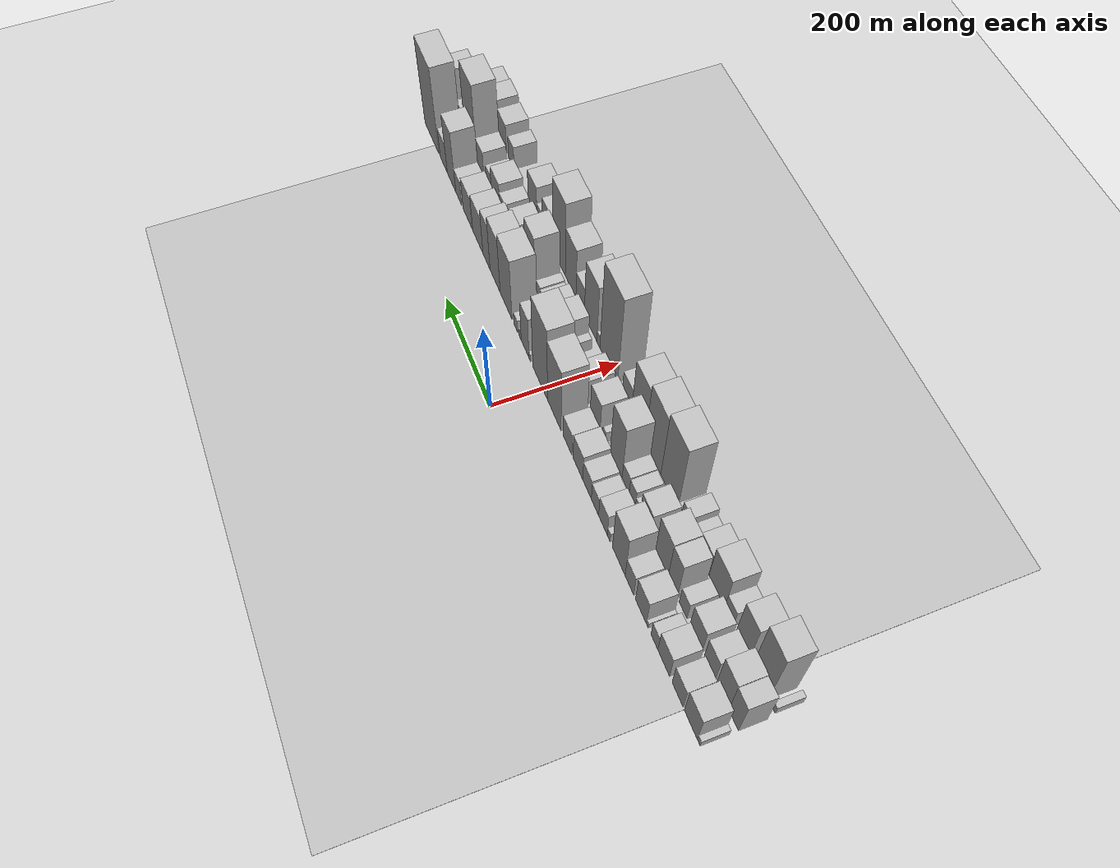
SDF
<?xml version="1.0" encoding="utf-8"?>

<sdf version="1.6">

   <world name="default">

      <gui fullscreen="0">

         <camera name="user_camera">

            <pose>-15 0 4.57585 0 0 0</pose>

            <view_controller>orbit</view_controller>

         </camera>

      </gui>

      <scene>

         <sky>

           <clouds>

             <speed>12</speed>

           </clouds>

         </sky>

         <ambient>0.4 0.4 0.4 1</ambient>

         <background>0.7 0.7 0.7 1</background>

         <shadows>1</shadows>

      </scene>

      <gravity>0 0 -9.8066</gravity>

      <magnetic_field>6e-06 2.3e-05 -4.2e-05</magnetic_field>

      <physics default="0" name="default_physics" type="ode">

         <ode>

            <solver>

               <type>quick</type>

               <iters>10</iters>

               <sor>1.0</sor>

               <use_dynamic_moi_rescaling>0</use_dynamic_moi_rescaling>

            </solver>

            <constraints>

               <cfm>0</cfm>

               <erp>0.2</erp>

               <contact_max_correcting_vel>100</contact_max_correcting_vel>

               <contact_surface_layer>0.001</contact_surface_layer>

            </constraints>

         </ode>

         <max_step_size>0.004</max_step_size>

         <real_time_factor>1</real_time_factor>

         <real_time_update_rate>250</real_time_update_rate>

      </physics>

      <light name="sun" type="directional">

         <cast_shadows>1</cast_shadows>

         <pose>0 0 10 0 0 0</pose>

         <diffuse>0.8 0.8 0.8 1</diffuse>

         <specular>0.2 0.2 0.2 1</specular>

         <attenuation>

            <range>1000</range>

            <constant>0.9</constant>

            <linear>0.01</linear>

            <quadratic>0.001</quadratic>

         </attenuation>

         <direction>-0.5 0.1 -0.9</direction>

      </light>

      <include>

         <name>ground_plane_1</name>

         <uri>model://HANNAS_ground_plane</uri>

         <pose>0 0 0  0 0 0</pose>

      </include>

      <include>

         <name>ground_plane_2</name>

         <uri>model://HANNAS_ground_plane</uri>

         <pose>100 0 0  0 0 0</pose>

      </include>

      <model name="building_1">

         <static>1</static>

         <pose frame="">100.0000 -543.5680 0 0.000000 0.000000 0.000000</pose>

         <link name="link">

            <pose frame="">0 0 9.00 0 0 0</pose>

            <collision name="collision">

               <geometry>

                  <box>

                     <size>40.0000 8.8639 18.0000</size>

                  </box>

               </geometry>

               <max_contacts>10</max_contacts>

               <surface>

                  <contact>

                     <ode/>

                  </contact>

                  <bounce/>

                  <friction>

                     <torsional>

                        <ode/>

                     </torsional>

                     <ode/>

                  </friction>

               </surface>

            </collision>

            <visual name="visual">

               <cast_shadows>0</cast_shadows>

               <geometry>

                  <box>

                     <size>40.0000 8.8639 18.0000</size>

                  </box>

               </geometry>

               <material>

                  <script>

                     <uri>model://HANNAS_wall/materials/scripts</uri>

                     <uri>model://HANNAS_wall/materials/textures</uri>

                     <name>vrc/HANNAS_wall</name>

                  </script>

               </material>

            </visual>

            <self_collide>0</self_collide>

            <enable_wind>0</enable_wind>

            <kinematic>0</kinematic>

         </link>

      </model>

      <model name="building_2">

         <static>1</static>

         <pose frame="">100.0000 -519.7971 0 0.000000 0.000000 0.000000</pose>

         <link name="link">

            <pose frame="">0 0 37.50 0 0 0</pose>

            <collision name="collision">

               <geometry>

                  <box>

                     <size>40.0000 38.6779 75.0000</size>

                  </box>

               </geometry>

               <max_contacts>10</max_contacts>

               <surface>

                  <contact>

                     <ode/>

                  </contact>

                  <bounce/>

                  <friction>

                     <torsional>

                        <ode/>

                     </torsional>

                     <ode/>

                  </friction>

               </surface>

            </collision>

            <visual name="visual">

               <cast_shadows>0</cast_shadows>

               <geometry>

                  <box>

                     <size>40.0000 38.6779 75.0000</size>

                  </box>

               </geometry>

               <material>

                  <script>

                     <uri>model://HANNAS_wall/materials/scripts</uri>

                     <uri>model://HANNAS_wall/materials/textures</uri>

                     <name>vrc/HANNAS_wall</name>

                  </script>

               </material>

            </visual>

            <self_collide>0</self_collide>

            <enable_wind>0</enable_wind>

            <kinematic>0</kinematic>

         </link>

      </model>

      <model name="building_3">

         <static>1</static>

         <pose frame="">100.0000 -479.5643 0 0.000000 0.000000 0.000000</pose>

         <link name="link">

            <pose frame="">0 0 30.00 0 0 0</pose>

            <collision name="collision">

               <geometry>

                  <box>

                     <size>40.0000 33.7877 60.0000</size>

                  </box>

               </geometry>

               <max_contacts>10</max_contacts>

               <surface>

                  <contact>

                     <ode/>

                  </contact>

                  <bounce/>

                  <friction>

                     <torsional>

                        <ode/>

                     </torsional>

                     <ode/>

                  </friction>

               </surface>

            </collision>

            <visual name="visual">

               <cast_shadows>0</cast_shadows>

               <geometry>

                  <box>

                     <size>40.0000 33.7877 60.0000</size>

                  </box>

               </geometry>

               <material>

                  <script>

                     <uri>model://HANNAS_wall/materials/scripts</uri>

                     <uri>model://HANNAS_wall/materials/textures</uri>

                     <name>vrc/HANNAS_wall</name>

                  </script>

               </material>

            </visual>

            <self_collide>0</self_collide>

            <enable_wind>0</enable_wind>

            <kinematic>0</kinematic>

         </link>

      </model>

      <model name="building_4">

         <static>1</static>

         <pose frame="">100.0000 -436.0321 0 0.000000 0.000000 0.000000</pose>

         <link name="link">

            <pose frame="">0 0 31.50 0 0 0</pose>

            <collision name="collision">

               <geometry>

                  <box>

                     <size>40.0000 37.2767 63.0000</size>

                  </box>

               </geometry>

               <max_contacts>10</max_contacts>

               <surface>

                  <contact>

                     <ode/>

                  </contact>

                  <bounce/>

                  <friction>

                     <torsional>

                        <ode/>

                     </torsional>

                     <ode/>

                  </friction>

               </surface>

            </collision>

            <visual name="visual">

               <cast_shadows>0</cast_shadows>

               <geometry>

                  <box>

                     <size>40.0000 37.2767 63.0000</size>

                  </box>

               </geometry>

               <material>

                  <script>

                     <uri>model://HANNAS_wall/materials/scripts</uri>

                     <uri>model://HANNAS_wall/materials/textures</uri>

                     <name>vrc/HANNAS_wall</name>

                  </script>

               </material>

            </visual>

            <self_collide>0</self_collide>

            <enable_wind>0</enable_wind>

            <kinematic>0</kinematic>

         </link>

      </model>

      <model name="building_5">

         <static>1</static>

         <pose frame="">100.0000 -406.3224 0 0.000000 0.000000 0.000000</pose>

         <link name="link">

            <pose frame="">0 0 21.00 0 0 0</pose>

            <collision name="collision">

               <geometry>

                  <box>

                     <size>40.0000 22.1427 42.0000</size>

                  </box>

               </geometry>

               <max_contacts>10</max_contacts>

               <surface>

                  <contact>

                     <ode/>

                  </contact>

                  <bounce/>

                  <friction>

                     <torsional>

                        <ode/>

                     </torsional>

                     <ode/>

                  </friction>

               </surface>

            </collision>

            <visual name="visual">

               <cast_shadows>0</cast_shadows>

               <geometry>

                  <box>

                     <size>40.0000 22.1427 42.0000</size>

                  </box>

               </geometry>

               <material>

                  <script>

                     <uri>model://HANNAS_wall/materials/scripts</uri>

                     <uri>model://HANNAS_wall/materials/textures</uri>

                     <name>vrc/HANNAS_wall</name>

                  </script>

               </material>

            </visual>

            <self_collide>0</self_collide>

            <enable_wind>0</enable_wind>

            <kinematic>0</kinematic>

         </link>

      </model>

      <model name="building_6">

         <static>1</static>

         <pose frame="">100.0000 -383.1758 0 0.000000 0.000000 0.000000</pose>

         <link name="link">

            <pose frame="">0 0 7.50 0 0 0</pose>

            <collision name="collision">

               <geometry>

                  <box>

                     <size>40.0000 6.1504 15.0000</size>

                  </box>

               </geometry>

               <max_contacts>10</max_contacts>

               <surface>

                  <contact>

                     <ode/>

                  </contact>

                  <bounce/>

                  <friction>

                     <torsional>

                        <ode/>

                     </torsional>

                     <ode/>

                  </friction>

               </surface>

            </collision>

            <visual name="visual">

               <cast_shadows>0</cast_shadows>

               <geometry>

                  <box>

                     <size>40.0000 6.1504 15.0000</size>

                  </box>

               </geometry>

               <material>

                  <script>

                     <uri>model://HANNAS_wall/materials/scripts</uri>

                     <uri>model://HANNAS_wall/materials/textures</uri>

                     <name>vrc/HANNAS_wall</name>

                  </script>

               </material>

            </visual>

            <self_collide>0</self_collide>

            <enable_wind>0</enable_wind>

            <kinematic>0</kinematic>

         </link>

      </model>

      <model name="building_7">

         <static>1</static>

         <pose frame="">100.0000 -362.1694 0 0.000000 0.000000 0.000000</pose>

         <link name="link">

            <pose frame="">0 0 34.50 0 0 0</pose>

            <collision name="collision">

               <geometry>

                  <box>

                     <size>40.0000 35.8624 69.0000</size>

                  </box>

               </geometry>

               <max_contacts>10</max_contacts>

               <surface>

                  <contact>

                     <ode/>

                  </contact>

                  <bounce/>

                  <friction>

                     <torsional>

                        <ode/>

                     </torsional>

                     <ode/>

                  </friction>

               </surface>

            </collision>

            <visual name="visual">

               <cast_shadows>0</cast_shadows>

               <geometry>

                  <box>

                     <size>40.0000 35.8624 69.0000</size>

                  </box>

               </geometry>

               <material>

                  <script>

                     <uri>model://HANNAS_wall/materials/scripts</uri>

                     <uri>model://HANNAS_wall/materials/textures</uri>

                     <name>vrc/HANNAS_wall</name>

                  </script>

               </material>

            </visual>

            <self_collide>0</self_collide>

            <enable_wind>0</enable_wind>

            <kinematic>0</kinematic>

         </link>

      </model>

      <model name="building_8">

         <static>1</static>

         <pose frame="">100.0000 -323.6770 0 0.000000 0.000000 0.000000</pose>

         <link name="link">

            <pose frame="">0 0 28.50 0 0 0</pose>

            <collision name="collision">

               <geometry>

                  <box>

                     <size>40.0000 29.1222 57.0000</size>

                  </box>

               </geometry>

               <max_contacts>10</max_contacts>

               <surface>

                  <contact>

                     <ode/>

                  </contact>

                  <bounce/>

                  <friction>

                     <torsional>

                        <ode/>

                     </torsional>

                     <ode/>

                  </friction>

               </surface>

            </collision>

            <visual name="visual">

               <cast_shadows>0</cast_shadows>

               <geometry>

                  <box>

                     <size>40.0000 29.1222 57.0000</size>

                  </box>

               </geometry>

               <material>

                  <script>

                     <uri>model://HANNAS_wall/materials/scripts</uri>

                     <uri>model://HANNAS_wall/materials/textures</uri>

                     <name>vrc/HANNAS_wall</name>

                  </script>

               </material>

            </visual>

            <self_collide>0</self_collide>

            <enable_wind>0</enable_wind>

            <kinematic>0</kinematic>

         </link>

      </model>

      <model name="building_9">

         <static>1</static>

         <pose frame="">100.0000 -287.0079 0 0.000000 0.000000 0.000000</pose>

         <link name="link">

            <pose frame="">0 0 57.00 0 0 0</pose>

            <collision name="collision">

               <geometry>

                  <box>

                     <size>40.0000 44.2160 114.0000</size>

                  </box>

               </geometry>

               <max_contacts>10</max_contacts>

               <surface>

                  <contact>

                     <ode/>

                  </contact>

                  <bounce/>

                  <friction>

                     <torsional>

                        <ode/>

                     </torsional>

                     <ode/>

                  </friction>

               </surface>

            </collision>

            <visual name="visual">

               <cast_shadows>0</cast_shadows>

               <geometry>

                  <box>

                     <size>40.0000 44.2160 114.0000</size>

                  </box>

               </geometry>

               <material>

                  <script>

                     <uri>model://HANNAS_wall/materials/scripts</uri>

                     <uri>model://HANNAS_wall/materials/textures</uri>

                     <name>vrc/HANNAS_wall</name>

                  </script>

               </material>

            </visual>

            <self_collide>0</self_collide>

            <enable_wind>0</enable_wind>

            <kinematic>0</kinematic>

         </link>

      </model>

      <model name="building_10">

         <static>1</static>

         <pose frame="">100.0000 -251.7439 0 0.000000 0.000000 0.000000</pose>

         <link name="link">

            <pose frame="">0 0 12.00 0 0 0</pose>

            <collision name="collision">

               <geometry>

                  <box>

                     <size>40.0000 10.3121 24.0000</size>

                  </box>

               </geometry>

               <max_contacts>10</max_contacts>

               <surface>

                  <contact>

                     <ode/>

                  </contact>

                  <bounce/>

                  <friction>

                     <torsional>

                        <ode/>

                     </torsional>

                     <ode/>

                  </friction>

               </surface>

            </collision>

            <visual name="visual">

               <cast_shadows>0</cast_shadows>

               <geometry>

                  <box>

                     <size>40.0000 10.3121 24.0000</size>

                  </box>

               </geometry>

               <material>

                  <script>

                     <uri>model://HANNAS_wall/materials/scripts</uri>

                     <uri>model://HANNAS_wall/materials/textures</uri>

                     <name>vrc/HANNAS_wall</name>

                  </script>

               </material>

            </visual>

            <self_collide>0</self_collide>

            <enable_wind>0</enable_wind>

            <kinematic>0</kinematic>

         </link>

      </model>

      <model name="building_11">

         <static>1</static>

         <pose frame="">100.0000 -231.2185 0 0.000000 0.000000 0.000000</pose>

         <link name="link">

            <pose frame="">0 0 28.50 0 0 0</pose>

            <collision name="collision">

               <geometry>

                  <box>

                     <size>40.0000 30.7387 57.0000</size>

                  </box>

               </geometry>

               <max_contacts>10</max_contacts>

               <surface>

                  <contact>

                     <ode/>

                  </contact>

                  <bounce/>

                  <friction>

                     <torsional>

                        <ode/>

                     </torsional>

                     <ode/>

                  </friction>

               </surface>

            </collision>

            <visual name="visual">

               <cast_shadows>0</cast_shadows>

               <geometry>

                  <box>

                     <size>40.0000 30.7387 57.0000</size>

                  </box>

               </geometry>

               <material>

                  <script>

                     <uri>model://HANNAS_wall/materials/scripts</uri>

                     <uri>model://HANNAS_wall/materials/textures</uri>

                     <name>vrc/HANNAS_wall</name>

                  </script>

               </material>

            </visual>

            <self_collide>0</self_collide>

            <enable_wind>0</enable_wind>

            <kinematic>0</kinematic>

         </link>

      </model>

      <model name="building_12">

         <static>1</static>

         <pose frame="">100.0000 -202.5148 0 0.000000 0.000000 0.000000</pose>

         <link name="link">

            <pose frame="">0 0 24.00 0 0 0</pose>

            <collision name="collision">

               <geometry>

                  <box>

                     <size>40.0000 26.6686 48.0000</size>

                  </box>

               </geometry>

               <max_contacts>10</max_contacts>

               <surface>

                  <contact>

                     <ode/>

                  </contact>

                  <bounce/>

                  <friction>

                     <torsional>

                        <ode/>

                     </torsional>

                     <ode/>

                  </friction>

               </surface>

            </collision>

            <visual name="visual">

               <cast_shadows>0</cast_shadows>

               <geometry>

                  <box>

                     <size>40.0000 26.6686 48.0000</size>

                  </box>

               </geometry>

               <material>

                  <script>

                     <uri>model://HANNAS_wall/materials/scripts</uri>

                     <uri>model://HANNAS_wall/materials/textures</uri>

                     <name>vrc/HANNAS_wall</name>

                  </script>

               </material>

            </visual>

            <self_collide>0</self_collide>

            <enable_wind>0</enable_wind>

            <kinematic>0</kinematic>

         </link>

      </model>

      <model name="building_13">

         <static>1</static>

         <pose frame="">100.0000 -173.3997 0 0.000000 0.000000 0.000000</pose>

         <link name="link">

            <pose frame="">0 0 27.00 0 0 0</pose>

            <collision name="collision">

               <geometry>

                  <box>

                     <size>40.0000 31.5617 54.0000</size>

                  </box>

               </geometry>

               <max_contacts>10</max_contacts>

               <surface>

                  <contact>

                     <ode/>

                  </contact>

                  <bounce/>

                  <friction>

                     <torsional>

                        <ode/>

                     </torsional>

                     <ode/>

                  </friction>

               </surface>

            </collision>

            <visual name="visual">

               <cast_shadows>0</cast_shadows>

               <geometry>

                  <box>

                     <size>40.0000 31.5617 54.0000</size>

                  </box>

               </geometry>

               <material>

                  <script>

                     <uri>model://HANNAS_wall/materials/scripts</uri>

                     <uri>model://HANNAS_wall/materials/textures</uri>

                     <name>vrc/HANNAS_wall</name>

                  </script>

               </material>

            </visual>

            <self_collide>0</self_collide>

            <enable_wind>0</enable_wind>

            <kinematic>0</kinematic>

         </link>

      </model>

      <model name="building_14">

         <static>1</static>

         <pose frame="">100.0000 -139.2445 0 0.000000 0.000000 0.000000</pose>

         <link name="link">

            <pose frame="">0 0 33.00 0 0 0</pose>

            <collision name="collision">

               <geometry>

                  <box>

                     <size>40.0000 36.7486 66.0000</size>

                  </box>

               </geometry>

               <max_contacts>10</max_contacts>

               <surface>

                  <contact>

                     <ode/>

                  </contact>

                  <bounce/>

                  <friction>

                     <torsional>

                        <ode/>

                     </torsional>

                     <ode/>

                  </friction>

               </surface>

            </collision>

            <visual name="visual">

               <cast_shadows>0</cast_shadows>

               <geometry>

                  <box>

                     <size>40.0000 36.7486 66.0000</size>

                  </box>

               </geometry>

               <material>

                  <script>

                     <uri>model://HANNAS_wall/materials/scripts</uri>

                     <uri>model://HANNAS_wall/materials/textures</uri>

                     <name>vrc/HANNAS_wall</name>

                  </script>

               </material>

            </visual>

            <self_collide>0</self_collide>

            <enable_wind>0</enable_wind>

            <kinematic>0</kinematic>

         </link>

      </model>

      <model name="building_15">

         <static>1</static>

         <pose frame="">100.0000 -99.0441 0 0.000000 0.000000 0.000000</pose>

         <link name="link">

            <pose frame="">0 0 28.50 0 0 0</pose>

            <collision name="collision">

               <geometry>

                  <box>

                     <size>40.0000 33.6522 57.0000</size>

                  </box>

               </geometry>

               <max_contacts>10</max_contacts>

               <surface>

                  <contact>

                     <ode/>

                  </contact>

                  <bounce/>

                  <friction>

                     <torsional>

                        <ode/>

                     </torsional>

                     <ode/>

                  </friction>

               </surface>

            </collision>

            <visual name="visual">

               <cast_shadows>0</cast_shadows>

               <geometry>

                  <box>

                     <size>40.0000 33.6522 57.0000</size>

                  </box>

               </geometry>

               <material>

                  <script>

                     <uri>model://HANNAS_wall/materials/scripts</uri>

                     <uri>model://HANNAS_wall/materials/textures</uri>

                     <name>vrc/HANNAS_wall</name>

                  </script>

               </material>

            </visual>

            <self_collide>0</self_collide>

            <enable_wind>0</enable_wind>

            <kinematic>0</kinematic>

         </link>

      </model>

      <model name="building_16">

         <static>1</static>

         <pose frame="">100.0000 -47.2371 0 0.000000 0.000000 0.000000</pose>

         <link name="link">

            <pose frame="">0 0 78.00 0 0 0</pose>

            <collision name="collision">

               <geometry>

                  <box>

                     <size>40.0000 53.9619 156.0000</size>

                  </box>

               </geometry>

               <max_contacts>10</max_contacts>

               <surface>

                  <contact>

                     <ode/>

                  </contact>

                  <bounce/>

                  <friction>

                     <torsional>

                        <ode/>

                     </torsional>

                     <ode/>

                  </friction>

               </surface>

            </collision>

            <visual name="visual">

               <cast_shadows>0</cast_shadows>

               <geometry>

                  <box>

                     <size>40.0000 53.9619 156.0000</size>

                  </box>

               </geometry>

               <material>

                  <script>

                     <uri>model://HANNAS_wall/materials/scripts</uri>

                     <uri>model://HANNAS_wall/materials/textures</uri>

                     <name>vrc/HANNAS_wall</name>

                  </script>

               </material>

            </visual>

            <self_collide>0</self_collide>

            <enable_wind>0</enable_wind>

            <kinematic>0</kinematic>

         </link>

      </model>

      <model name="building_17">

         <static>1</static>

         <pose frame="">100.0000 10.0317 0 0.000000 0.000000 0.000000</pose>

         <link name="link">

            <pose frame="">0 0 90.00 0 0 0</pose>

            <collision name="collision">

               <geometry>

                  <box>

                     <size>40.0000 60.5755 180.0000</size>

                  </box>

               </geometry>

               <max_contacts>10</max_contacts>

               <surface>

                  <contact>

                     <ode/>

                  </contact>

                  <bounce/>

                  <friction>

                     <torsional>

                        <ode/>

                     </torsional>

                     <ode/>

                  </friction>

               </surface>

            </collision>

            <visual name="visual">

               <cast_shadows>0</cast_shadows>

               <geometry>

                  <box>

                     <size>40.0000 60.5755 180.0000</size>

                  </box>

               </geometry>

               <material>

                  <script>

                     <uri>model://HANNAS_wall/materials/scripts</uri>

                     <uri>model://HANNAS_wall/materials/textures</uri>

                     <name>vrc/HANNAS_wall</name>

                  </script>

               </material>

            </visual>

            <self_collide>0</self_collide>

            <enable_wind>0</enable_wind>

            <kinematic>0</kinematic>

         </link>

      </model>

      <model name="building_18">

         <static>1</static>

         <pose frame="">100.0000 53.0055 0 0.000000 0.000000 0.000000</pose>

         <link name="link">

            <pose frame="">0 0 9.00 0 0 0</pose>

            <collision name="collision">

               <geometry>

                  <box>

                     <size>40.0000 7.3721 18.0000</size>

                  </box>

               </geometry>

               <max_contacts>10</max_contacts>

               <surface>

                  <contact>

                     <ode/>

                  </contact>

                  <bounce/>

                  <friction>

                     <torsional>

                        <ode/>

                     </torsional>

                     <ode/>

                  </friction>

               </surface>

            </collision>

            <visual name="visual">

               <cast_shadows>0</cast_shadows>

               <geometry>

                  <box>

                     <size>40.0000 7.3721 18.0000</size>

                  </box>

               </geometry>

               <material>

                  <script>

                     <uri>model://HANNAS_wall/materials/scripts</uri>

                     <uri>model://HANNAS_wall/materials/textures</uri>

                     <name>vrc/HANNAS_wall</name>

                  </script>

               </material>

            </visual>

            <self_collide>0</self_collide>

            <enable_wind>0</enable_wind>

            <kinematic>0</kinematic>

         </link>

      </model>

      <model name="building_19">

         <static>1</static>

         <pose frame="">100.0000 73.1179 0 0.000000 0.000000 0.000000</pose>

         <link name="link">

            <pose frame="">0 0 49.50 0 0 0</pose>

            <collision name="collision">

               <geometry>

                  <box>

                     <size>40.0000 32.8527 99.0000</size>

                  </box>

               </geometry>

               <max_contacts>10</max_contacts>

               <surface>

                  <contact>

                     <ode/>

                  </contact>

                  <bounce/>

                  <friction>

                     <torsional>

                        <ode/>

                     </torsional>

                     <ode/>

                  </friction>

               </surface>

            </collision>

            <visual name="visual">

               <cast_shadows>0</cast_shadows>

               <geometry>

                  <box>

                     <size>40.0000 32.8527 99.0000</size>

                  </box>

               </geometry>

               <material>

                  <script>

                     <uri>model://HANNAS_wall/materials/scripts</uri>

                     <uri>model://HANNAS_wall/materials/textures</uri>

                     <name>vrc/HANNAS_wall</name>

                  </script>

               </material>

            </visual>

            <self_collide>0</self_collide>

            <enable_wind>0</enable_wind>

            <kinematic>0</kinematic>

         </link>

      </model>

      <model name="building_20">

         <static>1</static>

         <pose frame="">100.0000 93.9917 0 0.000000 0.000000 0.000000</pose>

         <link name="link">

            <pose frame="">0 0 10.50 0 0 0</pose>

            <collision name="collision">

               <geometry>

                  <box>

                     <size>40.0000 8.8949 21.0000</size>

                  </box>

               </geometry>

               <max_contacts>10</max_contacts>

               <surface>

                  <contact>

                     <ode/>

                  </contact>

                  <bounce/>

                  <friction>

                     <torsional>

                        <ode/>

                     </torsional>

                     <ode/>

                  </friction>

               </surface>

            </collision>

            <visual name="visual">

               <cast_shadows>0</cast_shadows>

               <geometry>

                  <box>

                     <size>40.0000 8.8949 21.0000</size>

                  </box>

               </geometry>

               <material>

                  <script>

                     <uri>model://HANNAS_wall/materials/scripts</uri>

                     <uri>model://HANNAS_wall/materials/textures</uri>

                     <name>vrc/HANNAS_wall</name>

                  </script>

               </material>

            </visual>

            <self_collide>0</self_collide>

            <enable_wind>0</enable_wind>

            <kinematic>0</kinematic>

         </link>

      </model>

      <model name="building_21">

         <static>1</static>

         <pose frame="">100.0000 112.7230 0 0.000000 0.000000 0.000000</pose>

         <link name="link">

            <pose frame="">0 0 15.00 0 0 0</pose>

            <collision name="collision">

               <geometry>

                  <box>

                     <size>40.0000 16.5676 30.0000</size>

                  </box>

               </geometry>

               <max_contacts>10</max_contacts>

               <surface>

                  <contact>

                     <ode/>

                  </contact>

                  <bounce/>

                  <friction>

                     <torsional>

                        <ode/>

                     </torsional>

                     <ode/>

                  </friction>

               </surface>

            </collision>

            <visual name="visual">

               <cast_shadows>0</cast_shadows>

               <geometry>

                  <box>

                     <size>40.0000 16.5676 30.0000</size>

                  </box>

               </geometry>

               <material>

                  <script>

                     <uri>model://HANNAS_wall/materials/scripts</uri>

                     <uri>model://HANNAS_wall/materials/textures</uri>

                     <name>vrc/HANNAS_wall</name>

                  </script>

               </material>

            </visual>

            <self_collide>0</self_collide>

            <enable_wind>0</enable_wind>

            <kinematic>0</kinematic>

         </link>

      </model>

      <model name="building_22">

         <static>1</static>

         <pose frame="">100.0000 155.3587 0 0.000000 0.000000 0.000000</pose>

         <link name="link">

            <pose frame="">0 0 72.00 0 0 0</pose>

            <collision name="collision">

               <geometry>

                  <box>

                     <size>40.0000 52.7038 144.0000</size>

                  </box>

               </geometry>

               <max_contacts>10</max_contacts>

               <surface>

                  <contact>

                     <ode/>

                  </contact>

                  <bounce/>

                  <friction>

                     <torsional>

                        <ode/>

                     </torsional>

                     <ode/>

                  </friction>

               </surface>

            </collision>

            <visual name="visual">

               <cast_shadows>0</cast_shadows>

               <geometry>

                  <box>

                     <size>40.0000 52.7038 144.0000</size>

                  </box>

               </geometry>

               <material>

                  <script>

                     <uri>model://HANNAS_wall/materials/scripts</uri>

                     <uri>model://HANNAS_wall/materials/textures</uri>

                     <name>vrc/HANNAS_wall</name>

                  </script>

               </material>

            </visual>

            <self_collide>0</self_collide>

            <enable_wind>0</enable_wind>

            <kinematic>0</kinematic>

         </link>

      </model>

      <model name="building_23">

         <static>1</static>

         <pose frame="">100.0000 204.7117 0 0.000000 0.000000 0.000000</pose>

         <link name="link">

            <pose frame="">0 0 64.50 0 0 0</pose>

            <collision name="collision">

               <geometry>

                  <box>

                     <size>40.0000 46.0022 129.0000</size>

                  </box>

               </geometry>

               <max_contacts>10</max_contacts>

               <surface>

                  <contact>

                     <ode/>

                  </contact>

                  <bounce/>

                  <friction>

                     <torsional>

                        <ode/>

                     </torsional>

                     <ode/>

                  </friction>

               </surface>

            </collision>

            <visual name="visual">

               <cast_shadows>0</cast_shadows>

               <geometry>

                  <box>

                     <size>40.0000 46.0022 129.0000</size>

                  </box>

               </geometry>

               <material>

                  <script>

                     <uri>model://HANNAS_wall/materials/scripts</uri>

                     <uri>model://HANNAS_wall/materials/textures</uri>

                     <name>vrc/HANNAS_wall</name>

                  </script>

               </material>

            </visual>

            <self_collide>0</self_collide>

            <enable_wind>0</enable_wind>

            <kinematic>0</kinematic>

         </link>

      </model>

      <model name="building_24">

         <static>1</static>

         <pose frame="">100.0000 244.3947 0 0.000000 0.000000 0.000000</pose>

         <link name="link">

            <pose frame="">0 0 54.00 0 0 0</pose>

            <collision name="collision">

               <geometry>

                  <box>

                     <size>40.0000 33.3637 108.0000</size>

                  </box>

               </geometry>

               <max_contacts>10</max_contacts>

               <surface>

                  <contact>

                     <ode/>

                  </contact>

                  <bounce/>

                  <friction>

                     <torsional>

                        <ode/>

                     </torsional>

                     <ode/>

                  </friction>

               </surface>

            </collision>

            <visual name="visual">

               <cast_shadows>0</cast_shadows>

               <geometry>

                  <box>

                     <size>40.0000 33.3637 108.0000</size>

                  </box>

               </geometry>

               <material>

                  <script>

                     <uri>model://HANNAS_wall/materials/scripts</uri>

                     <uri>model://HANNAS_wall/materials/textures</uri>

                     <name>vrc/HANNAS_wall</name>

                  </script>

               </material>

            </visual>

            <self_collide>0</self_collide>

            <enable_wind>0</enable_wind>

            <kinematic>0</kinematic>

         </link>

      </model>

      <model name="building_25">

         <static>1</static>

         <pose frame="">100.0000 285.2390 0 0.000000 0.000000 0.000000</pose>

         <link name="link">

            <pose frame="">0 0 43.50 0 0 0</pose>

            <collision name="collision">

               <geometry>

                  <box>

                     <size>40.0000 48.3250 87.0000</size>

                  </box>

               </geometry>

               <max_contacts>10</max_contacts>

               <surface>

                  <contact>

                     <ode/>

                  </contact>

                  <bounce/>

                  <friction>

                     <torsional>

                        <ode/>

                     </torsional>

                     <ode/>

                  </friction>

               </surface>

            </collision>

            <visual name="visual">

               <cast_shadows>0</cast_shadows>

               <geometry>

                  <box>

                     <size>40.0000 48.3250 87.0000</size>

                  </box>

               </geometry>

               <material>

                  <script>

                     <uri>model://HANNAS_wall/materials/scripts</uri>

                     <uri>model://HANNAS_wall/materials/textures</uri>

                     <name>vrc/HANNAS_wall</name>

                  </script>

               </material>

            </visual>

            <self_collide>0</self_collide>

            <enable_wind>0</enable_wind>

            <kinematic>0</kinematic>

         </link>

      </model>

      <model name="building_26">

         <static>1</static>

         <pose frame="">100.0000 334.2590 0 0.000000 0.000000 0.000000</pose>

         <link name="link">

            <pose frame="">0 0 37.50 0 0 0</pose>

            <collision name="collision">

               <geometry>

                  <box>

                     <size>40.0000 43.7151 75.0000</size>

                  </box>

               </geometry>

               <max_contacts>10</max_contacts>

               <surface>

                  <contact>

                     <ode/>

                  </contact>

                  <bounce/>

                  <friction>

                     <torsional>

                        <ode/>

                     </torsional>

                     <ode/>

                  </friction>

               </surface>

            </collision>

            <visual name="visual">

               <cast_shadows>0</cast_shadows>

               <geometry>

                  <box>

                     <size>40.0000 43.7151 75.0000</size>

                  </box>

               </geometry>

               <material>

                  <script>

                     <uri>model://HANNAS_wall/materials/scripts</uri>

                     <uri>model://HANNAS_wall/materials/textures</uri>

                     <name>vrc/HANNAS_wall</name>

                  </script>

               </material>

            </visual>

            <self_collide>0</self_collide>

            <enable_wind>0</enable_wind>

            <kinematic>0</kinematic>

         </link>

      </model>

      <model name="building_27">

         <static>1</static>

         <pose frame="">100.0000 378.4005 0 0.000000 0.000000 0.000000</pose>

         <link name="link">

            <pose frame="">0 0 28.50 0 0 0</pose>

            <collision name="collision">

               <geometry>

                  <box>

                     <size>40.0000 28.5678 57.0000</size>

                  </box>

               </geometry>

               <max_contacts>10</max_contacts>

               <surface>

                  <contact>

                     <ode/>

                  </contact>

                  <bounce/>

                  <friction>

                     <torsional>

                        <ode/>

                     </torsional>

                     <ode/>

                  </friction>

               </surface>

            </collision>

            <visual name="visual">

               <cast_shadows>0</cast_shadows>

               <geometry>

                  <box>

                     <size>40.0000 28.5678 57.0000</size>

                  </box>

               </geometry>

               <material>

                  <script>

                     <uri>model://HANNAS_wall/materials/scripts</uri>

                     <uri>model://HANNAS_wall/materials/textures</uri>

                     <name>vrc/HANNAS_wall</name>

                  </script>

               </material>

            </visual>

            <self_collide>0</self_collide>

            <enable_wind>0</enable_wind>

            <kinematic>0</kinematic>

         </link>

      </model>

      <model name="building_28">

         <static>1</static>

         <pose frame="">100.0000 414.0339 0 0.000000 0.000000 0.000000</pose>

         <link name="link">

            <pose frame="">0 0 69.00 0 0 0</pose>

            <collision name="collision">

               <geometry>

                  <box>

                     <size>40.0000 42.6991 138.0000</size>

                  </box>

               </geometry>

               <max_contacts>10</max_contacts>

               <surface>

                  <contact>

                     <ode/>

                  </contact>

                  <bounce/>

                  <friction>

                     <torsional>

                        <ode/>

                     </torsional>

                     <ode/>

                  </friction>

               </surface>

            </collision>

            <visual name="visual">

               <cast_shadows>0</cast_shadows>

               <geometry>

                  <box>

                     <size>40.0000 42.6991 138.0000</size>

                  </box>

               </geometry>

               <material>

                  <script>

                     <uri>model://HANNAS_wall/materials/scripts</uri>

                     <uri>model://HANNAS_wall/materials/textures</uri>

                     <name>vrc/HANNAS_wall</name>

                  </script>

               </material>

            </visual>

            <self_collide>0</self_collide>

            <enable_wind>0</enable_wind>

            <kinematic>0</kinematic>

         </link>

      </model>

      <model name="building_29">

         <static>1</static>

         <pose frame="">100.0000 453.5905 0 0.000000 0.000000 0.000000</pose>

         <link name="link">

            <pose frame="">0 0 34.50 0 0 0</pose>

            <collision name="collision">

               <geometry>

                  <box>

                     <size>40.0000 36.4141 69.0000</size>

                  </box>

               </geometry>

               <max_contacts>10</max_contacts>

               <surface>

                  <contact>

                     <ode/>

                  </contact>

                  <bounce/>

                  <friction>

                     <torsional>

                        <ode/>

                     </torsional>

                     <ode/>

                  </friction>

               </surface>

            </collision>

            <visual name="visual">

               <cast_shadows>0</cast_shadows>

               <geometry>

                  <box>

                     <size>40.0000 36.4141 69.0000</size>

                  </box>

               </geometry>

               <material>

                  <script>

                     <uri>model://HANNAS_wall/materials/scripts</uri>

                     <uri>model://HANNAS_wall/materials/textures</uri>

                     <name>vrc/HANNAS_wall</name>

                  </script>

               </material>

            </visual>

            <self_collide>0</self_collide>

            <enable_wind>0</enable_wind>

            <kinematic>0</kinematic>

         </link>

      </model>

      <model name="building_30">

         <static>1</static>

         <pose frame="">100.0000 516.0462 0 0.000000 0.000000 0.000000</pose>

         <link name="link">

            <pose frame="">0 0 96.00 0 0 0</pose>

            <collision name="collision">

               <geometry>

                  <box>

                     <size>40.0000 74.4973 192.0000</size>

                  </box>

               </geometry>

               <max_contacts>10</max_contacts>

               <surface>

                  <contact>

                     <ode/>

                  </contact>

                  <bounce/>

                  <friction>

                     <torsional>

                        <ode/>

                     </torsional>

                     <ode/>

                  </friction>

               </surface>

            </collision>

            <visual name="visual">

               <cast_shadows>0</cast_shadows>

               <geometry>

                  <box>

                     <size>40.0000 74.4973 192.0000</size>

                  </box>

               </geometry>

               <material>

                  <script>

                     <uri>model://HANNAS_wall/materials/scripts</uri>

                     <uri>model://HANNAS_wall/materials/textures</uri>

                     <name>vrc/HANNAS_wall</name>

                  </script>

               </material>

            </visual>

            <self_collide>0</self_collide>

            <enable_wind>0</enable_wind>

            <kinematic>0</kinematic>

         </link>

      </model>

      <model name="building_31">

         <static>1</static>

         <pose frame="">152.0000 -533.9732 0 0.000000 0.000000 0.000000</pose>

         <link name="link">

            <pose frame="">0 0 46.50 0 0 0</pose>

            <collision name="collision">

               <geometry>

                  <box>

                     <size>40.0000 28.0535 93.0000</size>

                  </box>

               </geometry>

               <max_contacts>10</max_contacts>

               <surface>

                  <contact>

                     <ode/>

                  </contact>

                  <bounce/>

                  <friction>

                     <torsional>

                        <ode/>

                     </torsional>

                     <ode/>

                  </friction>

               </surface>

            </collision>

            <visual name="visual">

               <cast_shadows>0</cast_shadows>

               <geometry>

                  <box>

                     <size>40.0000 28.0535 93.0000</size>

                  </box>

               </geometry>

               <material>

                  <script>

                     <uri>model://HANNAS_wall/materials/scripts</uri>

                     <uri>model://HANNAS_wall/materials/textures</uri>

                     <name>vrc/HANNAS_wall</name>

                  </script>

               </material>

            </visual>

            <self_collide>0</self_collide>

            <enable_wind>0</enable_wind>

            <kinematic>0</kinematic>

         </link>

      </model>

      <model name="building_32">

         <static>1</static>

         <pose frame="">152.0000 -501.7975 0 0.000000 0.000000 0.000000</pose>

         <link name="link">

            <pose frame="">0 0 48.00 0 0 0</pose>

            <collision name="collision">

               <geometry>

                  <box>

                     <size>40.0000 36.2980 96.0000</size>

                  </box>

               </geometry>

               <max_contacts>10</max_contacts>

               <surface>

                  <contact>

                     <ode/>

                  </contact>

                  <bounce/>

                  <friction>

                     <torsional>

                        <ode/>

                     </torsional>

                     <ode/>

                  </friction>

               </surface>

            </collision>

            <visual name="visual">

               <cast_shadows>0</cast_shadows>

               <geometry>

                  <box>

                     <size>40.0000 36.2980 96.0000</size>

                  </box>

               </geometry>

               <material>

                  <script>

                     <uri>model://HANNAS_wall/materials/scripts</uri>

                     <uri>model://HANNAS_wall/materials/textures</uri>

                     <name>vrc/HANNAS_wall</name>

                  </script>

               </material>

            </visual>

            <self_collide>0</self_collide>

            <enable_wind>0</enable_wind>

            <kinematic>0</kinematic>

         </link>

      </model>

      <model name="building_33">

         <static>1</static>

         <pose frame="">152.0000 -463.0290 0 0.000000 0.000000 0.000000</pose>

         <link name="link">

            <pose frame="">0 0 31.50 0 0 0</pose>

            <collision name="collision">

               <geometry>

                  <box>

                     <size>40.0000 33.2391 63.0000</size>

                  </box>

               </geometry>

               <max_contacts>10</max_contacts>

               <surface>

                  <contact>

                     <ode/>

                  </contact>

                  <bounce/>

                  <friction>

                     <torsional>

                        <ode/>

                     </torsional>

                     <ode/>

                  </friction>

               </surface>

            </collision>

            <visual name="visual">

               <cast_shadows>0</cast_shadows>

               <geometry>

                  <box>

                     <size>40.0000 33.2391 63.0000</size>

                  </box>

               </geometry>

               <material>

                  <script>

                     <uri>model://HANNAS_wall/materials/scripts</uri>

                     <uri>model://HANNAS_wall/materials/textures</uri>

                     <name>vrc/HANNAS_wall</name>

                  </script>

               </material>

            </visual>

            <self_collide>0</self_collide>

            <enable_wind>0</enable_wind>

            <kinematic>0</kinematic>

         </link>

      </model>

      <model name="building_34">

         <static>1</static>

         <pose frame="">152.0000 -421.1633 0 0.000000 0.000000 0.000000</pose>

         <link name="link">

            <pose frame="">0 0 33.00 0 0 0</pose>

            <collision name="collision">

               <geometry>

                  <box>

                     <size>40.0000 38.4921 66.0000</size>

                  </box>

               </geometry>

               <max_contacts>10</max_contacts>

               <surface>

                  <contact>

                     <ode/>

                  </contact>

                  <bounce/>

                  <friction>

                     <torsional>

                        <ode/>

                     </torsional>

                     <ode/>

                  </friction>

               </surface>

            </collision>

            <visual name="visual">

               <cast_shadows>0</cast_shadows>

               <geometry>

                  <box>

                     <size>40.0000 38.4921 66.0000</size>

                  </box>

               </geometry>

               <material>

                  <script>

                     <uri>model://HANNAS_wall/materials/scripts</uri>

                     <uri>model://HANNAS_wall/materials/textures</uri>

                     <name>vrc/HANNAS_wall</name>

                  </script>

               </material>

            </visual>

            <self_collide>0</self_collide>

            <enable_wind>0</enable_wind>

            <kinematic>0</kinematic>

         </link>

      </model>

      <model name="building_35">

         <static>1</static>

         <pose frame="">152.0000 -380.5153 0 0.000000 0.000000 0.000000</pose>

         <link name="link">

            <pose frame="">0 0 24.00 0 0 0</pose>

            <collision name="collision">

               <geometry>

                  <box>

                     <size>40.0000 24.8040 48.0000</size>

                  </box>

               </geometry>

               <max_contacts>10</max_contacts>

               <surface>

                  <contact>

                     <ode/>

                  </contact>

                  <bounce/>

                  <friction>

                     <torsional>

                        <ode/>

                     </torsional>

                     <ode/>

                  </friction>

               </surface>

            </collision>

            <visual name="visual">

               <cast_shadows>0</cast_shadows>

               <geometry>

                  <box>

                     <size>40.0000 24.8040 48.0000</size>

                  </box>

               </geometry>

               <material>

                  <script>

                     <uri>model://HANNAS_wall/materials/scripts</uri>

                     <uri>model://HANNAS_wall/materials/textures</uri>

                     <name>vrc/HANNAS_wall</name>

                  </script>

               </material>

            </visual>

            <self_collide>0</self_collide>

            <enable_wind>0</enable_wind>

            <kinematic>0</kinematic>

         </link>

      </model>

      <model name="building_36">

         <static>1</static>

         <pose frame="">152.0000 -346.7919 0 0.000000 0.000000 0.000000</pose>

         <link name="link">

            <pose frame="">0 0 51.00 0 0 0</pose>

            <collision name="collision">

               <geometry>

                  <box>

                     <size>40.0000 30.6427 102.0000</size>

                  </box>

               </geometry>

               <max_contacts>10</max_contacts>

               <surface>

                  <contact>

                     <ode/>

                  </contact>

                  <bounce/>

                  <friction>

                     <torsional>

                        <ode/>

                     </torsional>

                     <ode/>

                  </friction>

               </surface>

            </collision>

            <visual name="visual">

               <cast_shadows>0</cast_shadows>

               <geometry>

                  <box>

                     <size>40.0000 30.6427 102.0000</size>

                  </box>

               </geometry>

               <material>

                  <script>

                     <uri>model://HANNAS_wall/materials/scripts</uri>

                     <uri>model://HANNAS_wall/materials/textures</uri>

                     <name>vrc/HANNAS_wall</name>

                  </script>

               </material>

            </visual>

            <self_collide>0</self_collide>

            <enable_wind>0</enable_wind>

            <kinematic>0</kinematic>

         </link>

      </model>

      <model name="building_37">

         <static>1</static>

         <pose frame="">152.0000 -311.0156 0 0.000000 0.000000 0.000000</pose>

         <link name="link">

            <pose frame="">0 0 52.50 0 0 0</pose>

            <collision name="collision">

               <geometry>

                  <box>

                     <size>40.0000 40.9099 105.0000</size>

                  </box>

               </geometry>

               <max_contacts>10</max_contacts>

               <surface>

                  <contact>

                     <ode/>

                  </contact>

                  <bounce/>

                  <friction>

                     <torsional>

                        <ode/>

                     </torsional>

                     <ode/>

                  </friction>

               </surface>

            </collision>

            <visual name="visual">

               <cast_shadows>0</cast_shadows>

               <geometry>

                  <box>

                     <size>40.0000 40.9099 105.0000</size>

                  </box>

               </geometry>

               <material>

                  <script>

                     <uri>model://HANNAS_wall/materials/scripts</uri>

                     <uri>model://HANNAS_wall/materials/textures</uri>

                     <name>vrc/HANNAS_wall</name>

                  </script>

               </material>

            </visual>

            <self_collide>0</self_collide>

            <enable_wind>0</enable_wind>

            <kinematic>0</kinematic>

         </link>

      </model>

      <model name="building_38">

         <static>1</static>

         <pose frame="">152.0000 -285.9816 0 0.000000 0.000000 0.000000</pose>

         <link name="link">

            <pose frame="">0 0 10.50 0 0 0</pose>

            <collision name="collision">

               <geometry>

                  <box>

                     <size>40.0000 9.1581 21.0000</size>

                  </box>

               </geometry>

               <max_contacts>10</max_contacts>

               <surface>

                  <contact>

                     <ode/>

                  </contact>

                  <bounce/>

                  <friction>

                     <torsional>

                        <ode/>

                     </torsional>

                     <ode/>

                  </friction>

               </surface>

            </collision>

            <visual name="visual">

               <cast_shadows>0</cast_shadows>

               <geometry>

                  <box>

                     <size>40.0000 9.1581 21.0000</size>

                  </box>

               </geometry>

               <material>

                  <script>

                     <uri>model://HANNAS_wall/materials/scripts</uri>

                     <uri>model://HANNAS_wall/materials/textures</uri>

                     <name>vrc/HANNAS_wall</name>

                  </script>

               </material>

            </visual>

            <self_collide>0</self_collide>

            <enable_wind>0</enable_wind>

            <kinematic>0</kinematic>

         </link>

      </model>

      <model name="building_39">

         <static>1</static>

         <pose frame="">152.0000 -255.1567 0 0.000000 0.000000 0.000000</pose>

         <link name="link">

            <pose frame="">0 0 36.00 0 0 0</pose>

            <collision name="collision">

               <geometry>

                  <box>

                     <size>40.0000 36.4918 72.0000</size>

                  </box>

               </geometry>

               <max_contacts>10</max_contacts>

               <surface>

                  <contact>

                     <ode/>

                  </contact>

                  <bounce/>

                  <friction>

                     <torsional>

                        <ode/>

                     </torsional>

                     <ode/>

                  </friction>

               </surface>

            </collision>

            <visual name="visual">

               <cast_shadows>0</cast_shadows>

               <geometry>

                  <box>

                     <size>40.0000 36.4918 72.0000</size>

                  </box>

               </geometry>

               <material>

                  <script>

                     <uri>model://HANNAS_wall/materials/scripts</uri>

                     <uri>model://HANNAS_wall/materials/textures</uri>

                     <name>vrc/HANNAS_wall</name>

                  </script>

               </material>

            </visual>

            <self_collide>0</self_collide>

            <enable_wind>0</enable_wind>

            <kinematic>0</kinematic>

         </link>

      </model>

      <model name="building_40">

         <static>1</static>

         <pose frame="">152.0000 -227.0851 0 0.000000 0.000000 0.000000</pose>

         <link name="link">

            <pose frame="">0 0 13.50 0 0 0</pose>

            <collision name="collision">

               <geometry>

                  <box>

                     <size>40.0000 11.6513 27.0000</size>

                  </box>

               </geometry>

               <max_contacts>10</max_contacts>

               <surface>

                  <contact>

                     <ode/>

                  </contact>

                  <bounce/>

                  <friction>

                     <torsional>

                        <ode/>

                     </torsional>

                     <ode/>

                  </friction>

               </surface>

            </collision>

            <visual name="visual">

               <cast_shadows>0</cast_shadows>

               <geometry>

                  <box>

                     <size>40.0000 11.6513 27.0000</size>

                  </box>

               </geometry>

               <material>

                  <script>

                     <uri>model://HANNAS_wall/materials/scripts</uri>

                     <uri>model://HANNAS_wall/materials/textures</uri>

                     <name>vrc/HANNAS_wall</name>

                  </script>

               </material>

            </visual>

            <self_collide>0</self_collide>

            <enable_wind>0</enable_wind>

            <kinematic>0</kinematic>

         </link>

      </model>

      <model name="building_41">

         <static>1</static>

         <pose frame="">152.0000 -210.3361 0 0.000000 0.000000 0.000000</pose>

         <link name="link">

            <pose frame="">0 0 21.00 0 0 0</pose>

            <collision name="collision">

               <geometry>

                  <box>

                     <size>40.0000 21.8468 42.0000</size>

                  </box>

               </geometry>

               <max_contacts>10</max_contacts>

               <surface>

                  <contact>

                     <ode/>

                  </contact>

                  <bounce/>

                  <friction>

                     <torsional>

                        <ode/>

                     </torsional>

                     <ode/>

                  </friction>

               </surface>

            </collision>

            <visual name="visual">

               <cast_shadows>0</cast_shadows>

               <geometry>

                  <box>

                     <size>40.0000 21.8468 42.0000</size>

                  </box>

               </geometry>

               <material>

                  <script>

                     <uri>model://HANNAS_wall/materials/scripts</uri>

                     <uri>model://HANNAS_wall/materials/textures</uri>

                     <name>vrc/HANNAS_wall</name>

                  </script>

               </material>

            </visual>

            <self_collide>0</self_collide>

            <enable_wind>0</enable_wind>

            <kinematic>0</kinematic>

         </link>

      </model>

      <model name="building_42">

         <static>1</static>

         <pose frame="">152.0000 -186.9256 0 0.000000 0.000000 0.000000</pose>

         <link name="link">

            <pose frame="">0 0 22.50 0 0 0</pose>

            <collision name="collision">

               <geometry>

                  <box>

                     <size>40.0000 24.9743 45.0000</size>

                  </box>

               </geometry>

               <max_contacts>10</max_contacts>

               <surface>

                  <contact>

                     <ode/>

                  </contact>

                  <bounce/>

                  <friction>

                     <torsional>

                        <ode/>

                     </torsional>

                     <ode/>

                  </friction>

               </surface>

            </collision>

            <visual name="visual">

               <cast_shadows>0</cast_shadows>

               <geometry>

                  <box>

                     <size>40.0000 24.9743 45.0000</size>

                  </box>

               </geometry>

               <material>

                  <script>

                     <uri>model://HANNAS_wall/materials/scripts</uri>

                     <uri>model://HANNAS_wall/materials/textures</uri>

                     <name>vrc/HANNAS_wall</name>

                  </script>

               </material>

            </visual>

            <self_collide>0</self_collide>

            <enable_wind>0</enable_wind>

            <kinematic>0</kinematic>

         </link>

      </model>

      <model name="building_43">

         <static>1</static>

         <pose frame="">152.0000 -152.5429 0 0.000000 0.000000 0.000000</pose>

         <link name="link">

            <pose frame="">0 0 67.50 0 0 0</pose>

            <collision name="collision">

               <geometry>

                  <box>

                     <size>40.0000 43.7910 135.0000</size>

                  </box>

               </geometry>

               <max_contacts>10</max_contacts>

               <surface>

                  <contact>

                     <ode/>

                  </contact>

                  <bounce/>

                  <friction>

                     <torsional>

                        <ode/>

                     </torsional>

                     <ode/>

                  </friction>

               </surface>

            </collision>

            <visual name="visual">

               <cast_shadows>0</cast_shadows>

               <geometry>

                  <box>

                     <size>40.0000 43.7910 135.0000</size>

                  </box>

               </geometry>

               <material>

                  <script>

                     <uri>model://HANNAS_wall/materials/scripts</uri>

                     <uri>model://HANNAS_wall/materials/textures</uri>

                     <name>vrc/HANNAS_wall</name>

                  </script>

               </material>

            </visual>

            <self_collide>0</self_collide>

            <enable_wind>0</enable_wind>

            <kinematic>0</kinematic>

         </link>

      </model>

      <model name="building_44">

         <static>1</static>

         <pose frame="">152.0000 -127.3507 0 0.000000 0.000000 0.000000</pose>

         <link name="link">

            <pose frame="">0 0 7.50 0 0 0</pose>

            <collision name="collision">

               <geometry>

                  <box>

                     <size>40.0000 6.5933 15.0000</size>

                  </box>

               </geometry>

               <max_contacts>10</max_contacts>

               <surface>

                  <contact>

                     <ode/>

                  </contact>

                  <bounce/>

                  <friction>

                     <torsional>

                        <ode/>

                     </torsional>

                     <ode/>

                  </friction>

               </surface>

            </collision>

            <visual name="visual">

               <cast_shadows>0</cast_shadows>

               <geometry>

                  <box>

                     <size>40.0000 6.5933 15.0000</size>

                  </box>

               </geometry>

               <material>

                  <script>

                     <uri>model://HANNAS_wall/materials/scripts</uri>

                     <uri>model://HANNAS_wall/materials/textures</uri>

                     <name>vrc/HANNAS_wall</name>

                  </script>

               </material>

            </visual>

            <self_collide>0</self_collide>

            <enable_wind>0</enable_wind>

            <kinematic>0</kinematic>

         </link>

      </model>

      <model name="building_45">

         <static>1</static>

         <pose frame="">152.0000 -108.3668 0 0.000000 0.000000 0.000000</pose>

         <link name="link">

            <pose frame="">0 0 13.50 0 0 0</pose>

            <collision name="collision">

               <geometry>

                  <box>

                     <size>40.0000 11.3746 27.0000</size>

                  </box>

               </geometry>

               <max_contacts>10</max_contacts>

               <surface>

                  <contact>

                     <ode/>

                  </contact>

                  <bounce/>

                  <friction>

                     <torsional>

                        <ode/>

                     </torsional>

                     <ode/>

                  </friction>

               </surface>

            </collision>

            <visual name="visual">

               <cast_shadows>0</cast_shadows>

               <geometry>

                  <box>

                     <size>40.0000 11.3746 27.0000</size>

                  </box>

               </geometry>

               <material>

                  <script>

                     <uri>model://HANNAS_wall/materials/scripts</uri>

                     <uri>model://HANNAS_wall/materials/textures</uri>

                     <name>vrc/HANNAS_wall</name>

                  </script>

               </material>

            </visual>

            <self_collide>0</self_collide>

            <enable_wind>0</enable_wind>

            <kinematic>0</kinematic>

         </link>

      </model>

      <model name="building_46">

         <static>1</static>

         <pose frame="">152.0000 -75.0782 0 0.000000 0.000000 0.000000</pose>

         <link name="link">

            <pose frame="">0 0 34.50 0 0 0</pose>

            <collision name="collision">

               <geometry>

                  <box>

                     <size>40.0000 37.2026 69.0000</size>

                  </box>

               </geometry>

               <max_contacts>10</max_contacts>

               <surface>

                  <contact>

                     <ode/>

                  </contact>

                  <bounce/>

                  <friction>

                     <torsional>

                        <ode/>

                     </torsional>

                     <ode/>

                  </friction>

               </surface>

            </collision>

            <visual name="visual">

               <cast_shadows>0</cast_shadows>

               <geometry>

                  <box>

                     <size>40.0000 37.2026 69.0000</size>

                  </box>

               </geometry>

               <material>

                  <script>

                     <uri>model://HANNAS_wall/materials/scripts</uri>

                     <uri>model://HANNAS_wall/materials/textures</uri>

                     <name>vrc/HANNAS_wall</name>

                  </script>

               </material>

            </visual>

            <self_collide>0</self_collide>

            <enable_wind>0</enable_wind>

            <kinematic>0</kinematic>

         </link>

      </model>

      <model name="building_47">

         <static>1</static>

         <pose frame="">152.0000 -29.1522 0 0.000000 0.000000 0.000000</pose>

         <link name="link">

            <pose frame="">0 0 31.50 0 0 0</pose>

            <collision name="collision">

               <geometry>

                  <box>

                     <size>40.0000 36.6495 63.0000</size>

                  </box>

               </geometry>

               <max_contacts>10</max_contacts>

               <surface>

                  <contact>

                     <ode/>

                  </contact>

                  <bounce/>

                  <friction>

                     <torsional>

                        <ode/>

                     </torsional>

                     <ode/>

                  </friction>

               </surface>

            </collision>

            <visual name="visual">

               <cast_shadows>0</cast_shadows>

               <geometry>

                  <box>

                     <size>40.0000 36.6495 63.0000</size>

                  </box>

               </geometry>

               <material>

                  <script>

                     <uri>model://HANNAS_wall/materials/scripts</uri>

                     <uri>model://HANNAS_wall/materials/textures</uri>

                     <name>vrc/HANNAS_wall</name>

                  </script>

               </material>

            </visual>

            <self_collide>0</self_collide>

            <enable_wind>0</enable_wind>

            <kinematic>0</kinematic>

         </link>

      </model>

      <model name="building_48">

         <static>1</static>

         <pose frame="">152.0000 44.2119 0 0.000000 0.000000 0.000000</pose>

         <link name="link">

            <pose frame="">0 0 13.50 0 0 0</pose>

            <collision name="collision">

               <geometry>

                  <box>

                     <size>40.0000 13.3596 27.0000</size>

                  </box>

               </geometry>

               <max_contacts>10</max_contacts>

               <surface>

                  <contact>

                     <ode/>

                  </contact>

                  <bounce/>

                  <friction>

                     <torsional>

                        <ode/>

                     </torsional>

                     <ode/>

                  </friction>

               </surface>

            </collision>

            <visual name="visual">

               <cast_shadows>0</cast_shadows>

               <geometry>

                  <box>

                     <size>40.0000 13.3596 27.0000</size>

                  </box>

               </geometry>

               <material>

                  <script>

                     <uri>model://HANNAS_wall/materials/scripts</uri>

                     <uri>model://HANNAS_wall/materials/textures</uri>

                     <name>vrc/HANNAS_wall</name>

                  </script>

               </material>

            </visual>

            <self_collide>0</self_collide>

            <enable_wind>0</enable_wind>

            <kinematic>0</kinematic>

         </link>

      </model>

      <model name="building_49">

         <static>1</static>

         <pose frame="">152.0000 71.4884 0 0.000000 0.000000 0.000000</pose>

         <link name="link">

            <pose frame="">0 0 34.50 0 0 0</pose>

            <collision name="collision">

               <geometry>

                  <box>

                     <size>40.0000 41.1933 69.0000</size>

                  </box>

               </geometry>

               <max_contacts>10</max_contacts>

               <surface>

                  <contact>

                     <ode/>

                  </contact>

                  <bounce/>

                  <friction>

                     <torsional>

                        <ode/>

                     </torsional>

                     <ode/>

                  </friction>

               </surface>

            </collision>

            <visual name="visual">

               <cast_shadows>0</cast_shadows>

               <geometry>

                  <box>

                     <size>40.0000 41.1933 69.0000</size>

                  </box>

               </geometry>

               <material>

                  <script>

                     <uri>model://HANNAS_wall/materials/scripts</uri>

                     <uri>model://HANNAS_wall/materials/textures</uri>

                     <name>vrc/HANNAS_wall</name>

                  </script>

               </material>

            </visual>

            <self_collide>0</self_collide>

            <enable_wind>0</enable_wind>

            <kinematic>0</kinematic>

         </link>

      </model>

      <model name="building_50">

         <static>1</static>

         <pose frame="">152.0000 95.3189 0 0.000000 0.000000 0.000000</pose>

         <link name="link">

            <pose frame="">0 0 7.50 0 0 0</pose>

            <collision name="collision">

               <geometry>

                  <box>

                     <size>40.0000 6.4677 15.0000</size>

                  </box>

               </geometry>

               <max_contacts>10</max_contacts>

               <surface>

                  <contact>

                     <ode/>

                  </contact>

                  <bounce/>

                  <friction>

                     <torsional>

                        <ode/>

                     </torsional>

                     <ode/>

                  </friction>

               </surface>

            </collision>

            <visual name="visual">

               <cast_shadows>0</cast_shadows>

               <geometry>

                  <box>

                     <size>40.0000 6.4677 15.0000</size>

                  </box>

               </geometry>

               <material>

                  <script>

                     <uri>model://HANNAS_wall/materials/scripts</uri>

                     <uri>model://HANNAS_wall/materials/textures</uri>

                     <name>vrc/HANNAS_wall</name>

                  </script>

               </material>

            </visual>

            <self_collide>0</self_collide>

            <enable_wind>0</enable_wind>

            <kinematic>0</kinematic>

         </link>

      </model>

      <model name="building_51">

         <static>1</static>

         <pose frame="">152.0000 115.4108 0 0.000000 0.000000 0.000000</pose>

         <link name="link">

            <pose frame="">0 0 24.00 0 0 0</pose>

            <collision name="collision">

               <geometry>

                  <box>

                     <size>40.0000 25.7161 48.0000</size>

                  </box>

               </geometry>

               <max_contacts>10</max_contacts>

               <surface>

                  <contact>

                     <ode/>

                  </contact>

                  <bounce/>

                  <friction>

                     <torsional>

                        <ode/>

                     </torsional>

                     <ode/>

                  </friction>

               </surface>

            </collision>

            <visual name="visual">

               <cast_shadows>0</cast_shadows>

               <geometry>

                  <box>

                     <size>40.0000 25.7161 48.0000</size>

                  </box>

               </geometry>

               <material>

                  <script>

                     <uri>model://HANNAS_wall/materials/scripts</uri>

                     <uri>model://HANNAS_wall/materials/textures</uri>

                     <name>vrc/HANNAS_wall</name>

                  </script>

               </material>

            </visual>

            <self_collide>0</self_collide>

            <enable_wind>0</enable_wind>

            <kinematic>0</kinematic>

         </link>

      </model>

      <model name="building_52">

         <static>1</static>

         <pose frame="">152.0000 141.4687 0 0.000000 0.000000 0.000000</pose>

         <link name="link">

            <pose frame="">0 0 13.50 0 0 0</pose>

            <collision name="collision">

               <geometry>

                  <box>

                     <size>40.0000 12.3997 27.0000</size>

                  </box>

               </geometry>

               <max_contacts>10</max_contacts>

               <surface>

                  <contact>

                     <ode/>

                  </contact>

                  <bounce/>

                  <friction>

                     <torsional>

                        <ode/>

                     </torsional>

                     <ode/>

                  </friction>

               </surface>

            </collision>

            <visual name="visual">

               <cast_shadows>0</cast_shadows>

               <geometry>

                  <box>

                     <size>40.0000 12.3997 27.0000</size>

                  </box>

               </geometry>

               <material>

                  <script>

                     <uri>model://HANNAS_wall/materials/scripts</uri>

                     <uri>model://HANNAS_wall/materials/textures</uri>

                     <name>vrc/HANNAS_wall</name>

                  </script>

               </material>

            </visual>

            <self_collide>0</self_collide>

            <enable_wind>0</enable_wind>

            <kinematic>0</kinematic>

         </link>

      </model>

      <model name="building_53">

         <static>1</static>

         <pose frame="">152.0000 156.0027 0 0.000000 0.000000 0.000000</pose>

         <link name="link">

            <pose frame="">0 0 15.00 0 0 0</pose>

            <collision name="collision">

               <geometry>

                  <box>

                     <size>40.0000 16.6683 30.0000</size>

                  </box>

               </geometry>

               <max_contacts>10</max_contacts>

               <surface>

                  <contact>

                     <ode/>

                  </contact>

                  <bounce/>

                  <friction>

                     <torsional>

                        <ode/>

                     </torsional>

                     <ode/>

                  </friction>

               </surface>

            </collision>

            <visual name="visual">

               <cast_shadows>0</cast_shadows>

               <geometry>

                  <box>

                     <size>40.0000 16.6683 30.0000</size>

                  </box>

               </geometry>

               <material>

                  <script>

                     <uri>model://HANNAS_wall/materials/scripts</uri>

                     <uri>model://HANNAS_wall/materials/textures</uri>

                     <name>vrc/HANNAS_wall</name>

                  </script>

               </material>

            </visual>

            <self_collide>0</self_collide>

            <enable_wind>0</enable_wind>

            <kinematic>0</kinematic>

         </link>

      </model>

      <model name="building_54">

         <static>1</static>

         <pose frame="">152.0000 190.8599 0 0.000000 0.000000 0.000000</pose>

         <link name="link">

            <pose frame="">0 0 61.50 0 0 0</pose>

            <collision name="collision">

               <geometry>

                  <box>

                     <size>40.0000 43.0461 123.0000</size>

                  </box>

               </geometry>

               <max_contacts>10</max_contacts>

               <surface>

                  <contact>

                     <ode/>

                  </contact>

                  <bounce/>

                  <friction>

                     <torsional>

                        <ode/>

                     </torsional>

                     <ode/>

                  </friction>

               </surface>

            </collision>

            <visual name="visual">

               <cast_shadows>0</cast_shadows>

               <geometry>

                  <box>

                     <size>40.0000 43.0461 123.0000</size>

                  </box>

               </geometry>

               <material>

                  <script>

                     <uri>model://HANNAS_wall/materials/scripts</uri>

                     <uri>model://HANNAS_wall/materials/textures</uri>

                     <name>vrc/HANNAS_wall</name>

                  </script>

               </material>

            </visual>

            <self_collide>0</self_collide>

            <enable_wind>0</enable_wind>

            <kinematic>0</kinematic>

         </link>

      </model>

      <model name="building_55">

         <static>1</static>

         <pose frame="">152.0000 233.0276 0 0.000000 0.000000 0.000000</pose>

         <link name="link">

            <pose frame="">0 0 22.50 0 0 0</pose>

            <collision name="collision">

               <geometry>

                  <box>

                     <size>40.0000 25.2893 45.0000</size>

                  </box>

               </geometry>

               <max_contacts>10</max_contacts>

               <surface>

                  <contact>

                     <ode/>

                  </contact>

                  <bounce/>

                  <friction>

                     <torsional>

                        <ode/>

                     </torsional>

                     <ode/>

                  </friction>

               </surface>

            </collision>

            <visual name="visual">

               <cast_shadows>0</cast_shadows>

               <geometry>

                  <box>

                     <size>40.0000 25.2893 45.0000</size>

                  </box>

               </geometry>

               <material>

                  <script>

                     <uri>model://HANNAS_wall/materials/scripts</uri>

                     <uri>model://HANNAS_wall/materials/textures</uri>

                     <name>vrc/HANNAS_wall</name>

                  </script>

               </material>

            </visual>

            <self_collide>0</self_collide>

            <enable_wind>0</enable_wind>

            <kinematic>0</kinematic>

         </link>

      </model>

      <model name="building_56">

         <static>1</static>

         <pose frame="">152.0000 264.1108 0 0.000000 0.000000 0.000000</pose>

         <link name="link">

            <pose frame="">0 0 31.50 0 0 0</pose>

            <collision name="collision">

               <geometry>

                  <box>

                     <size>40.0000 36.8770 63.0000</size>

                  </box>

               </geometry>

               <max_contacts>10</max_contacts>

               <surface>

                  <contact>

                     <ode/>

                  </contact>

                  <bounce/>

                  <friction>

                     <torsional>

                        <ode/>

                     </torsional>

                     <ode/>

                  </friction>

               </surface>

            </collision>

            <visual name="visual">

               <cast_shadows>0</cast_shadows>

               <geometry>

                  <box>

                     <size>40.0000 36.8770 63.0000</size>

                  </box>

               </geometry>

               <material>

                  <script>

                     <uri>model://HANNAS_wall/materials/scripts</uri>

                     <uri>model://HANNAS_wall/materials/textures</uri>

                     <name>vrc/HANNAS_wall</name>

                  </script>

               </material>

            </visual>

            <self_collide>0</self_collide>

            <enable_wind>0</enable_wind>

            <kinematic>0</kinematic>

         </link>

      </model>

      <model name="building_57">

         <static>1</static>

         <pose frame="">152.0000 291.1768 0 0.000000 0.000000 0.000000</pose>

         <link name="link">

            <pose frame="">0 0 16.50 0 0 0</pose>

            <collision name="collision">

               <geometry>

                  <box>

                     <size>40.0000 17.2550 33.0000</size>

                  </box>

               </geometry>

               <max_contacts>10</max_contacts>

               <surface>

                  <contact>

                     <ode/>

                  </contact>

                  <bounce/>

                  <friction>

                     <torsional>

                        <ode/>

                     </torsional>

                     <ode/>

                  </friction>

               </surface>

            </collision>

            <visual name="visual">

               <cast_shadows>0</cast_shadows>

               <geometry>

                  <box>

                     <size>40.0000 17.2550 33.0000</size>

                  </box>

               </geometry>

               <material>

                  <script>

                     <uri>model://HANNAS_wall/materials/scripts</uri>

                     <uri>model://HANNAS_wall/materials/textures</uri>

                     <name>vrc/HANNAS_wall</name>

                  </script>

               </material>

            </visual>

            <self_collide>0</self_collide>

            <enable_wind>0</enable_wind>

            <kinematic>0</kinematic>

         </link>

      </model>

      <model name="building_58">

         <static>1</static>

         <pose frame="">152.0000 313.3842 0 0.000000 0.000000 0.000000</pose>

         <link name="link">

            <pose frame="">0 0 25.50 0 0 0</pose>

            <collision name="collision">

               <geometry>

                  <box>

                     <size>40.0000 27.1597 51.0000</size>

                  </box>

               </geometry>

               <max_contacts>10</max_contacts>

               <surface>

                  <contact>

                     <ode/>

                  </contact>

                  <bounce/>

                  <friction>

                     <torsional>

                        <ode/>

                     </torsional>

                     <ode/>

                  </friction>

               </surface>

            </collision>

            <visual name="visual">

               <cast_shadows>0</cast_shadows>

               <geometry>

                  <box>

                     <size>40.0000 27.1597 51.0000</size>

                  </box>

               </geometry>

               <material>

                  <script>

                     <uri>model://HANNAS_wall/materials/scripts</uri>

                     <uri>model://HANNAS_wall/materials/textures</uri>

                     <name>vrc/HANNAS_wall</name>

                  </script>

               </material>

            </visual>

            <self_collide>0</self_collide>

            <enable_wind>0</enable_wind>

            <kinematic>0</kinematic>

         </link>

      </model>

      <model name="building_59">

         <static>1</static>

         <pose frame="">152.0000 347.2046 0 0.000000 0.000000 0.000000</pose>

         <link name="link">

            <pose frame="">0 0 34.50 0 0 0</pose>

            <collision name="collision">

               <geometry>

                  <box>

                     <size>40.0000 40.4812 69.0000</size>

                  </box>

               </geometry>

               <max_contacts>10</max_contacts>

               <surface>

                  <contact>

                     <ode/>

                  </contact>

                  <bounce/>

                  <friction>

                     <torsional>

                        <ode/>

                     </torsional>

                     <ode/>

                  </friction>

               </surface>

            </collision>

            <visual name="visual">

               <cast_shadows>0</cast_shadows>

               <geometry>

                  <box>

                     <size>40.0000 40.4812 69.0000</size>

                  </box>

               </geometry>

               <material>

                  <script>

                     <uri>model://HANNAS_wall/materials/scripts</uri>

                     <uri>model://HANNAS_wall/materials/textures</uri>

                     <name>vrc/HANNAS_wall</name>

                  </script>

               </material>

            </visual>

            <self_collide>0</self_collide>

            <enable_wind>0</enable_wind>

            <kinematic>0</kinematic>

         </link>

      </model>

      <model name="building_60">

         <static>1</static>

         <pose frame="">152.0000 380.1130 0 0.000000 0.000000 0.000000</pose>

         <link name="link">

            <pose frame="">0 0 22.50 0 0 0</pose>

            <collision name="collision">

               <geometry>

                  <box>

                     <size>40.0000 25.3355 45.0000</size>

                  </box>

               </geometry>

               <max_contacts>10</max_contacts>

               <surface>

                  <contact>

                     <ode/>

                  </contact>

                  <bounce/>

                  <friction>

                     <torsional>

                        <ode/>

                     </torsional>

                     <ode/>

                  </friction>

               </surface>

            </collision>

            <visual name="visual">

               <cast_shadows>0</cast_shadows>

               <geometry>

                  <box>

                     <size>40.0000 25.3355 45.0000</size>

                  </box>

               </geometry>

               <material>

                  <script>

                     <uri>model://HANNAS_wall/materials/scripts</uri>

                     <uri>model://HANNAS_wall/materials/textures</uri>

                     <name>vrc/HANNAS_wall</name>

                  </script>

               </material>

            </visual>

            <self_collide>0</self_collide>

            <enable_wind>0</enable_wind>

            <kinematic>0</kinematic>

         </link>

      </model>

      <model name="building_61">

         <static>1</static>

         <pose frame="">152.0000 396.1754 0 0.000000 0.000000 0.000000</pose>

         <link name="link">

            <pose frame="">0 0 7.50 0 0 0</pose>

            <collision name="collision">

               <geometry>

                  <box>

                     <size>40.0000 6.7892 15.0000</size>

                  </box>

               </geometry>

               <max_contacts>10</max_contacts>

               <surface>

                  <contact>

                     <ode/>

                  </contact>

                  <bounce/>

                  <friction>

                     <torsional>

                        <ode/>

                     </torsional>

                     <ode/>

                  </friction>

               </surface>

            </collision>

            <visual name="visual">

               <cast_shadows>0</cast_shadows>

               <geometry>

                  <box>

                     <size>40.0000 6.7892 15.0000</size>

                  </box>

               </geometry>

               <material>

                  <script>

                     <uri>model://HANNAS_wall/materials/scripts</uri>

                     <uri>model://HANNAS_wall/materials/textures</uri>

                     <name>vrc/HANNAS_wall</name>

                  </script>

               </material>

            </visual>

            <self_collide>0</self_collide>

            <enable_wind>0</enable_wind>

            <kinematic>0</kinematic>

         </link>

      </model>

      <model name="building_62">

         <static>1</static>

         <pose frame="">152.0000 421.6604 0 0.000000 0.000000 0.000000</pose>

         <link name="link">

            <pose frame="">0 0 30.00 0 0 0</pose>

            <collision name="collision">

               <geometry>

                  <box>

                     <size>40.0000 34.1808 60.0000</size>

                  </box>

               </geometry>

               <max_contacts>10</max_contacts>

               <surface>

                  <contact>

                     <ode/>

                  </contact>

                  <bounce/>

                  <friction>

                     <torsional>

                        <ode/>

                     </torsional>

                     <ode/>

                  </friction>

               </surface>

            </collision>

            <visual name="visual">

               <cast_shadows>0</cast_shadows>

               <geometry>

                  <box>

                     <size>40.0000 34.1808 60.0000</size>

                  </box>

               </geometry>

               <material>

                  <script>

                     <uri>model://HANNAS_wall/materials/scripts</uri>

                     <uri>model://HANNAS_wall/materials/textures</uri>

                     <name>vrc/HANNAS_wall</name>

                  </script>

               </material>

            </visual>

            <self_collide>0</self_collide>

            <enable_wind>0</enable_wind>

            <kinematic>0</kinematic>

         </link>

      </model>

      <model name="building_63">

         <static>1</static>

         <pose frame="">152.0000 467.5517 0 0.000000 0.000000 0.000000</pose>

         <link name="link">

            <pose frame="">0 0 87.00 0 0 0</pose>

            <collision name="collision">

               <geometry>

                  <box>

                     <size>40.0000 57.6016 174.0000</size>

                  </box>

               </geometry>

               <max_contacts>10</max_contacts>

               <surface>

                  <contact>

                     <ode/>

                  </contact>

                  <bounce/>

                  <friction>

                     <torsional>

                        <ode/>

                     </torsional>

                     <ode/>

                  </friction>

               </surface>

            </collision>

            <visual name="visual">

               <cast_shadows>0</cast_shadows>

               <geometry>

                  <box>

                     <size>40.0000 57.6016 174.0000</size>

                  </box>

               </geometry>

               <material>

                  <script>

                     <uri>model://HANNAS_wall/materials/scripts</uri>

                     <uri>model://HANNAS_wall/materials/textures</uri>

                     <name>vrc/HANNAS_wall</name>

                  </script>

               </material>

            </visual>

            <self_collide>0</self_collide>

            <enable_wind>0</enable_wind>

            <kinematic>0</kinematic>

         </link>

      </model>

      <model name="building_64">

         <static>1</static>

         <pose frame="">152.0000 501.2418 0 0.000000 0.000000 0.000000</pose>

         <link name="link">

            <pose frame="">0 0 10.50 0 0 0</pose>

            <collision name="collision">

               <geometry>

                  <box>

                     <size>40.0000 9.7786 21.0000</size>

                  </box>

               </geometry>

               <max_contacts>10</max_contacts>

               <surface>

                  <contact>

                     <ode/>

                  </contact>

                  <bounce/>

                  <friction>

                     <torsional>

                        <ode/>

                     </torsional>

                     <ode/>

                  </friction>

               </surface>

            </collision>

            <visual name="visual">

               <cast_shadows>0</cast_shadows>

               <geometry>

                  <box>

                     <size>40.0000 9.7786 21.0000</size>

                  </box>

               </geometry>

               <material>

                  <script>

                     <uri>model://HANNAS_wall/materials/scripts</uri>

                     <uri>model://HANNAS_wall/materials/textures</uri>

                     <name>vrc/HANNAS_wall</name>

                  </script>

               </material>

            </visual>

            <self_collide>0</self_collide>

            <enable_wind>0</enable_wind>

            <kinematic>0</kinematic>

         </link>

      </model>

      <model name="building_65">

         <static>1</static>

         <pose frame="">152.0000 521.1083 0 0.000000 0.000000 0.000000</pose>

         <link name="link">

            <pose frame="">0 0 25.50 0 0 0</pose>

            <collision name="collision">

               <geometry>

                  <box>

                     <size>40.0000 29.9545 51.0000</size>

                  </box>

               </geometry>

               <max_contacts>10</max_contacts>

               <surface>

                  <contact>

                     <ode/>

                  </contact>

                  <bounce/>

                  <friction>

                     <torsional>

                        <ode/>

                     </torsional>

                     <ode/>

                  </friction>

               </surface>

            </collision>

            <visual name="visual">

               <cast_shadows>0</cast_shadows>

               <geometry>

                  <box>

                     <size>40.0000 29.9545 51.0000</size>

                  </box>

               </geometry>

               <material>

                  <script>

                     <uri>model://HANNAS_wall/materials/scripts</uri>

                     <uri>model://HANNAS_wall/materials/textures</uri>

                     <name>vrc/HANNAS_wall</name>

                  </script>

               </material>

            </visual>

            <self_collide>0</self_collide>

            <enable_wind>0</enable_wind>

            <kinematic>0</kinematic>

         </link>

      </model>

      <model name="building_66">

         <static>1</static>

         <pose frame="">152.0000 564.1155 0 0.000000 0.000000 0.000000</pose>

         <link name="link">

            <pose frame="">0 0 54.00 0 0 0</pose>

            <collision name="collision">

               <geometry>

                  <box>

                     <size>40.0000 36.0598 108.0000</size>

                  </box>

               </geometry>

               <max_contacts>10</max_contacts>

               <surface>

                  <contact>

                     <ode/>

                  </contact>

                  <bounce/>

                  <friction>

                     <torsional>

                        <ode/>

                     </torsional>

                     <ode/>

                  </friction>

               </surface>

            </collision>

            <visual name="visual">

               <cast_shadows>0</cast_shadows>

               <geometry>

                  <box>

                     <size>40.0000 36.0598 108.0000</size>

                  </box>

               </geometry>

               <material>

                  <script>

                     <uri>model://HANNAS_wall/materials/scripts</uri>

                     <uri>model://HANNAS_wall/materials/textures</uri>

                     <name>vrc/HANNAS_wall</name>

                  </script>

               </material>

            </visual>

            <self_collide>0</self_collide>

            <enable_wind>0</enable_wind>

            <kinematic>0</kinematic>

         </link>

      </model>

      <model name="building_67">

         <static>1</static>

         <pose frame="">204.0000 -539.9155 0 0.000000 0.000000 0.000000</pose>

         <link name="link">

            <pose frame="">0 0 10.50 0 0 0</pose>

            <collision name="collision">

               <geometry>

                  <box>

                     <size>40.0000 10.1689 21.0000</size>

                  </box>

               </geometry>

               <max_contacts>10</max_contacts>

               <surface>

                  <contact>

                     <ode/>

                  </contact>

                  <bounce/>

                  <friction>

                     <torsional>

                        <ode/>

                     </torsional>

                     <ode/>

                  </friction>

               </surface>

            </collision>

            <visual name="visual">

               <cast_shadows>0</cast_shadows>

               <geometry>

                  <box>

                     <size>40.0000 10.1689 21.0000</size>

                  </box>

               </geometry>

               <material>

                  <script>

                     <uri>model://HANNAS_wall/materials/scripts</uri>

                     <uri>model://HANNAS_wall/materials/textures</uri>

                     <name>vrc/HANNAS_wall</name>

                  </script>

               </material>

            </visual>

            <self_collide>0</self_collide>

            <enable_wind>0</enable_wind>

            <kinematic>0</kinematic>

         </link>

      </model>

      <model name="building_68">

         <static>1</static>

         <pose frame="">204.0000 -502.8106 0 0.000000 0.000000 0.000000</pose>

         <link name="link">

            <pose frame="">0 0 73.50 0 0 0</pose>

            <collision name="collision">

               <geometry>

                  <box>

                     <size>40.0000 46.0410 147.0000</size>

                  </box>

               </geometry>

               <max_contacts>10</max_contacts>

               <surface>

                  <contact>

                     <ode/>

                  </contact>

                  <bounce/>

                  <friction>

                     <torsional>

                        <ode/>

                     </torsional>

                     <ode/>

                  </friction>

               </surface>

            </collision>

            <visual name="visual">

               <cast_shadows>0</cast_shadows>

               <geometry>

                  <box>

                     <size>40.0000 46.0410 147.0000</size>

                  </box>

               </geometry>

               <material>

                  <script>

                     <uri>model://HANNAS_wall/materials/scripts</uri>

                     <uri>model://HANNAS_wall/materials/textures</uri>

                     <name>vrc/HANNAS_wall</name>

                  </script>

               </material>

            </visual>

            <self_collide>0</self_collide>

            <enable_wind>0</enable_wind>

            <kinematic>0</kinematic>

         </link>

      </model>

      <model name="building_69">

         <static>1</static>

         <pose frame="">204.0000 -451.1943 0 0.000000 0.000000 0.000000</pose>

         <link name="link">

            <pose frame="">0 0 51.00 0 0 0</pose>

            <collision name="collision">

               <geometry>

                  <box>

                     <size>40.0000 39.1917 102.0000</size>

                  </box>

               </geometry>

               <max_contacts>10</max_contacts>

               <surface>

                  <contact>

                     <ode/>

                  </contact>

                  <bounce/>

                  <friction>

                     <torsional>

                        <ode/>

                     </torsional>

                     <ode/>

                  </friction>

               </surface>

            </collision>

            <visual name="visual">

               <cast_shadows>0</cast_shadows>

               <geometry>

                  <box>

                     <size>40.0000 39.1917 102.0000</size>

                  </box>

               </geometry>

               <material>

                  <script>

                     <uri>model://HANNAS_wall/materials/scripts</uri>

                     <uri>model://HANNAS_wall/materials/textures</uri>

                     <name>vrc/HANNAS_wall</name>

                  </script>

               </material>

            </visual>

            <self_collide>0</self_collide>

            <enable_wind>0</enable_wind>

            <kinematic>0</kinematic>

         </link>

      </model>

      <model name="building_70">

         <static>1</static>

         <pose frame="">204.0000 -410.2224 0 0.000000 0.000000 0.000000</pose>

         <link name="link">

            <pose frame="">0 0 22.50 0 0 0</pose>

            <collision name="collision">

               <geometry>

                  <box>

                     <size>40.0000 26.7520 45.0000</size>

                  </box>

               </geometry>

               <max_contacts>10</max_contacts>

               <surface>

                  <contact>

                     <ode/>

                  </contact>

                  <bounce/>

                  <friction>

                     <torsional>

                        <ode/>

                     </torsional>

                     <ode/>

                  </friction>

               </surface>

            </collision>

            <visual name="visual">

               <cast_shadows>0</cast_shadows>

               <geometry>

                  <box>

                     <size>40.0000 26.7520 45.0000</size>

                  </box>

               </geometry>

               <material>

                  <script>

                     <uri>model://HANNAS_wall/materials/scripts</uri>

                     <uri>model://HANNAS_wall/materials/textures</uri>

                     <name>vrc/HANNAS_wall</name>

                  </script>

               </material>

            </visual>

            <self_collide>0</self_collide>

            <enable_wind>0</enable_wind>

            <kinematic>0</kinematic>

         </link>

      </model>

      <model name="building_71">

         <static>1</static>

         <pose frame="">204.0000 -372.8732 0 0.000000 0.000000 0.000000</pose>

         <link name="link">

            <pose frame="">0 0 45.00 0 0 0</pose>

            <collision name="collision">

               <geometry>

                  <box>

                     <size>40.0000 47.9465 90.0000</size>

                  </box>

               </geometry>

               <max_contacts>10</max_contacts>

               <surface>

                  <contact>

                     <ode/>

                  </contact>

                  <bounce/>

                  <friction>

                     <torsional>

                        <ode/>

                     </torsional>

                     <ode/>

                  </friction>

               </surface>

            </collision>

            <visual name="visual">

               <cast_shadows>0</cast_shadows>

               <geometry>

                  <box>

                     <size>40.0000 47.9465 90.0000</size>

                  </box>

               </geometry>

               <material>

                  <script>

                     <uri>model://HANNAS_wall/materials/scripts</uri>

                     <uri>model://HANNAS_wall/materials/textures</uri>

                     <name>vrc/HANNAS_wall</name>

                  </script>

               </material>

            </visual>

            <self_collide>0</self_collide>

            <enable_wind>0</enable_wind>

            <kinematic>0</kinematic>

         </link>

      </model>

      <model name="building_72">

         <static>1</static>

         <pose frame="">204.0000 -330.6751 0 0.000000 0.000000 0.000000</pose>

         <link name="link">

            <pose frame="">0 0 31.50 0 0 0</pose>

            <collision name="collision">

               <geometry>

                  <box>

                     <size>40.0000 36.4496 63.0000</size>

                  </box>

               </geometry>

               <max_contacts>10</max_contacts>

               <surface>

                  <contact>

                     <ode/>

                  </contact>

                  <bounce/>

                  <friction>

                     <torsional>

                        <ode/>

                     </torsional>

                     <ode/>

                  </friction>

               </surface>

            </collision>

            <visual name="visual">

               <cast_shadows>0</cast_shadows>

               <geometry>

                  <box>

                     <size>40.0000 36.4496 63.0000</size>

                  </box>

               </geometry>

               <material>

                  <script>

                     <uri>model://HANNAS_wall/materials/scripts</uri>

                     <uri>model://HANNAS_wall/materials/textures</uri>

                     <name>vrc/HANNAS_wall</name>

                  </script>

               </material>

            </visual>

            <self_collide>0</self_collide>

            <enable_wind>0</enable_wind>

            <kinematic>0</kinematic>

         </link>

      </model>

      <model name="building_73">

         <static>1</static>

         <pose frame="">204.0000 -293.4745 0 0.000000 0.000000 0.000000</pose>

         <link name="link">

            <pose frame="">0 0 15.00 0 0 0</pose>

            <collision name="collision">

               <geometry>

                  <box>

                     <size>40.0000 17.9516 30.0000</size>

                  </box>

               </geometry>

               <max_contacts>10</max_contacts>

               <surface>

                  <contact>

                     <ode/>

                  </contact>

                  <bounce/>

                  <friction>

                     <torsional>

                        <ode/>

                     </torsional>

                     <ode/>

                  </friction>

               </surface>

            </collision>

            <visual name="visual">

               <cast_shadows>0</cast_shadows>

               <geometry>

                  <box>

                     <size>40.0000 17.9516 30.0000</size>

                  </box>

               </geometry>

               <material>

                  <script>

                     <uri>model://HANNAS_wall/materials/scripts</uri>

                     <uri>model://HANNAS_wall/materials/textures</uri>

                     <name>vrc/HANNAS_wall</name>

                  </script>

               </material>

            </visual>

            <self_collide>0</self_collide>

            <enable_wind>0</enable_wind>

            <kinematic>0</kinematic>

         </link>

      </model>

      <model name="building_74">

         <static>1</static>

         <pose frame="">204.0000 -271.2954 0 0.000000 0.000000 0.000000</pose>

         <link name="link">

            <pose frame="">0 0 24.00 0 0 0</pose>

            <collision name="collision">

               <geometry>

                  <box>

                     <size>40.0000 26.4065 48.0000</size>

                  </box>

               </geometry>

               <max_contacts>10</max_contacts>

               <surface>

                  <contact>

                     <ode/>

                  </contact>

                  <bounce/>

                  <friction>

                     <torsional>

                        <ode/>

                     </torsional>

                     <ode/>

                  </friction>

               </surface>

            </collision>

            <visual name="visual">

               <cast_shadows>0</cast_shadows>

               <geometry>

                  <box>

                     <size>40.0000 26.4065 48.0000</size>

                  </box>

               </geometry>

               <material>

                  <script>

                     <uri>model://HANNAS_wall/materials/scripts</uri>

                     <uri>model://HANNAS_wall/materials/textures</uri>

                     <name>vrc/HANNAS_wall</name>

                  </script>

               </material>

            </visual>

            <self_collide>0</self_collide>

            <enable_wind>0</enable_wind>

            <kinematic>0</kinematic>

         </link>

      </model>

      <model name="building_75">

         <static>1</static>

         <pose frame="">204.0000 -252.3435 0 0.000000 0.000000 0.000000</pose>

         <link name="link">

            <pose frame="">0 0 12.00 0 0 0</pose>

            <collision name="collision">

               <geometry>

                  <box>

                     <size>40.0000 11.4972 24.0000</size>

                  </box>

               </geometry>

               <max_contacts>10</max_contacts>

               <surface>

                  <contact>

                     <ode/>

                  </contact>

                  <bounce/>

                  <friction>

                     <torsional>

                        <ode/>

                     </torsional>

                     <ode/>

                  </friction>

               </surface>

            </collision>

            <visual name="visual">

               <cast_shadows>0</cast_shadows>

               <geometry>

                  <box>

                     <size>40.0000 11.4972 24.0000</size>

                  </box>

               </geometry>

               <material>

                  <script>

                     <uri>model://HANNAS_wall/materials/scripts</uri>

                     <uri>model://HANNAS_wall/materials/textures</uri>

                     <name>vrc/HANNAS_wall</name>

                  </script>

               </material>

            </visual>

            <self_collide>0</self_collide>

            <enable_wind>0</enable_wind>

            <kinematic>0</kinematic>

         </link>

      </model>

      <model name="building_76">

         <static>1</static>

         <pose frame="">204.0000 -217.8556 0 0.000000 0.000000 0.000000</pose>

         <link name="link">

            <pose frame="">0 0 85.50 0 0 0</pose>

            <collision name="collision">

               <geometry>

                  <box>

                     <size>40.0000 57.4786 171.0000</size>

                  </box>

               </geometry>

               <max_contacts>10</max_contacts>

               <surface>

                  <contact>

                     <ode/>

                  </contact>

                  <bounce/>

                  <friction>

                     <torsional>

                        <ode/>

                     </torsional>

                     <ode/>

                  </friction>

               </surface>

            </collision>

            <visual name="visual">

               <cast_shadows>0</cast_shadows>

               <geometry>

                  <box>

                     <size>40.0000 57.4786 171.0000</size>

                  </box>

               </geometry>

               <material>

                  <script>

                     <uri>model://HANNAS_wall/materials/scripts</uri>

                     <uri>model://HANNAS_wall/materials/textures</uri>

                     <name>vrc/HANNAS_wall</name>

                  </script>

               </material>

            </visual>

            <self_collide>0</self_collide>

            <enable_wind>0</enable_wind>

            <kinematic>0</kinematic>

         </link>

      </model>

      <model name="building_77">

         <static>1</static>

         <pose frame="">204.0000 -161.2896 0 0.000000 0.000000 0.000000</pose>

         <link name="link">

            <pose frame="">0 0 78.00 0 0 0</pose>

            <collision name="collision">

               <geometry>

                  <box>

                     <size>40.0000 55.6534 156.0000</size>

                  </box>

               </geometry>

               <max_contacts>10</max_contacts>

               <surface>

                  <contact>

                     <ode/>

                  </contact>

                  <bounce/>

                  <friction>

                     <torsional>

                        <ode/>

                     </torsional>

                     <ode/>

                  </friction>

               </surface>

            </collision>

            <visual name="visual">

               <cast_shadows>0</cast_shadows>

               <geometry>

                  <box>

                     <size>40.0000 55.6534 156.0000</size>

                  </box>

               </geometry>

               <material>

                  <script>

                     <uri>model://HANNAS_wall/materials/scripts</uri>

                     <uri>model://HANNAS_wall/materials/textures</uri>

                     <name>vrc/HANNAS_wall</name>

                  </script>

               </material>

            </visual>

            <self_collide>0</self_collide>

            <enable_wind>0</enable_wind>

            <kinematic>0</kinematic>

         </link>

      </model>

      <model name="building_78">

         <static>1</static>

         <pose frame="">204.0000 -108.6967 0 0.000000 0.000000 0.000000</pose>

         <link name="link">

            <pose frame="">0 0 70.50 0 0 0</pose>

            <collision name="collision">

               <geometry>

                  <box>

                     <size>40.0000 49.5323 141.0000</size>

                  </box>

               </geometry>

               <max_contacts>10</max_contacts>

               <surface>

                  <contact>

                     <ode/>

                  </contact>

                  <bounce/>

                  <friction>

                     <torsional>

                        <ode/>

                     </torsional>

                     <ode/>

                  </friction>

               </surface>

            </collision>

            <visual name="visual">

               <cast_shadows>0</cast_shadows>

               <geometry>

                  <box>

                     <size>40.0000 49.5323 141.0000</size>

                  </box>

               </geometry>

               <material>

                  <script>

                     <uri>model://HANNAS_wall/materials/scripts</uri>

                     <uri>model://HANNAS_wall/materials/textures</uri>

                     <name>vrc/HANNAS_wall</name>

                  </script>

               </material>

            </visual>

            <self_collide>0</self_collide>

            <enable_wind>0</enable_wind>

            <kinematic>0</kinematic>

         </link>

      </model>

      <model name="building_79">

         <static>1</static>

         <pose frame="">204.0000 -66.7433 0 0.000000 0.000000 0.000000</pose>

         <link name="link">

            <pose frame="">0 0 31.50 0 0 0</pose>

            <collision name="collision">

               <geometry>

                  <box>

                     <size>40.0000 34.3745 63.0000</size>

                  </box>

               </geometry>

               <max_contacts>10</max_contacts>

               <surface>

                  <contact>

                     <ode/>

                  </contact>

                  <bounce/>

                  <friction>

                     <torsional>

                        <ode/>

                     </torsional>

                     <ode/>

                  </friction>

               </surface>

            </collision>

            <visual name="visual">

               <cast_shadows>0</cast_shadows>

               <geometry>

                  <box>

                     <size>40.0000 34.3745 63.0000</size>

                  </box>

               </geometry>

               <material>

                  <script>

                     <uri>model://HANNAS_wall/materials/scripts</uri>

                     <uri>model://HANNAS_wall/materials/textures</uri>

                     <name>vrc/HANNAS_wall</name>

                  </script>

               </material>

            </visual>

            <self_collide>0</self_collide>

            <enable_wind>0</enable_wind>

            <kinematic>0</kinematic>

         </link>

      </model>

      <model name="building_80">

         <static>1</static>

         <pose frame="">204.0000 -40.1487 0 0.000000 0.000000 0.000000</pose>

         <link name="link">

            <pose frame="">0 0 7.50 0 0 0</pose>

            <collision name="collision">

               <geometry>

                  <box>

                     <size>40.0000 6.8147 15.0000</size>

                  </box>

               </geometry>

               <max_contacts>10</max_contacts>

               <surface>

                  <contact>

                     <ode/>

                  </contact>

                  <bounce/>

                  <friction>

                     <torsional>

                        <ode/>

                     </torsional>

                     <ode/>

                  </friction>

               </surface>

            </collision>

            <visual name="visual">

               <cast_shadows>0</cast_shadows>

               <geometry>

                  <box>

                     <size>40.0000 6.8147 15.0000</size>

                  </box>

               </geometry>

               <material>

                  <script>

                     <uri>model://HANNAS_wall/materials/scripts</uri>

                     <uri>model://HANNAS_wall/materials/textures</uri>

                     <name>vrc/HANNAS_wall</name>

                  </script>

               </material>

            </visual>

            <self_collide>0</self_collide>

            <enable_wind>0</enable_wind>

            <kinematic>0</kinematic>

         </link>

      </model>

      <model name="building_81">

         <static>1</static>

         <pose frame="">204.0000 1.1077 0 0.000000 0.000000 0.000000</pose>

         <link name="link">

            <pose frame="">0 0 106.50 0 0 0</pose>

            <collision name="collision">

               <geometry>

                  <box>

                     <size>40.0000 67.6982 213.0000</size>

                  </box>

               </geometry>

               <max_contacts>10</max_contacts>

               <surface>

                  <contact>

                     <ode/>

                  </contact>

                  <bounce/>

                  <friction>

                     <torsional>

                        <ode/>

                     </torsional>

                     <ode/>

                  </friction>

               </surface>

            </collision>

            <visual name="visual">

               <cast_shadows>0</cast_shadows>

               <geometry>

                  <box>

                     <size>40.0000 67.6982 213.0000</size>

                  </box>

               </geometry>

               <material>

                  <script>

                     <uri>model://HANNAS_wall/materials/scripts</uri>

                     <uri>model://HANNAS_wall/materials/textures</uri>

                     <name>vrc/HANNAS_wall</name>

                  </script>

               </material>

            </visual>

            <self_collide>0</self_collide>

            <enable_wind>0</enable_wind>

            <kinematic>0</kinematic>

         </link>

      </model>

      <model name="building_82">

         <static>1</static>

         <pose frame="">204.0000 41.0829 0 0.000000 0.000000 0.000000</pose>

         <link name="link">

            <pose frame="">0 0 13.50 0 0 0</pose>

            <collision name="collision">

               <geometry>

                  <box>

                     <size>40.0000 12.2522 27.0000</size>

                  </box>

               </geometry>

               <max_contacts>10</max_contacts>

               <surface>

                  <contact>

                     <ode/>

                  </contact>

                  <bounce/>

                  <friction>

                     <torsional>

                        <ode/>

                     </torsional>

                     <ode/>

                  </friction>

               </surface>

            </collision>

            <visual name="visual">

               <cast_shadows>0</cast_shadows>

               <geometry>

                  <box>

                     <size>40.0000 12.2522 27.0000</size>

                  </box>

               </geometry>

               <material>

                  <script>

                     <uri>model://HANNAS_wall/materials/scripts</uri>

                     <uri>model://HANNAS_wall/materials/textures</uri>

                     <name>vrc/HANNAS_wall</name>

                  </script>

               </material>

            </visual>

            <self_collide>0</self_collide>

            <enable_wind>0</enable_wind>

            <kinematic>0</kinematic>

         </link>

      </model>

      <model name="building_83">

         <static>1</static>

         <pose frame="">204.0000 72.1895 0 0.000000 0.000000 0.000000</pose>

         <link name="link">

            <pose frame="">0 0 67.50 0 0 0</pose>

            <collision name="collision">

               <geometry>

                  <box>

                     <size>40.0000 49.9611 135.0000</size>

                  </box>

               </geometry>

               <max_contacts>10</max_contacts>

               <surface>

                  <contact>

                     <ode/>

                  </contact>

                  <bounce/>

                  <friction>

                     <torsional>

                        <ode/>

                     </torsional>

                     <ode/>

                  </friction>

               </surface>

            </collision>

            <visual name="visual">

               <cast_shadows>0</cast_shadows>

               <geometry>

                  <box>

                     <size>40.0000 49.9611 135.0000</size>

                  </box>

               </geometry>

               <material>

                  <script>

                     <uri>model://HANNAS_wall/materials/scripts</uri>

                     <uri>model://HANNAS_wall/materials/textures</uri>

                     <name>vrc/HANNAS_wall</name>

                  </script>

               </material>

            </visual>

            <self_collide>0</self_collide>

            <enable_wind>0</enable_wind>

            <kinematic>0</kinematic>

         </link>

      </model>

      <model name="building_84">

         <static>1</static>

         <pose frame="">204.0000 114.3619 0 0.000000 0.000000 0.000000</pose>

         <link name="link">

            <pose frame="">0 0 33.00 0 0 0</pose>

            <collision name="collision">

               <geometry>

                  <box>

                     <size>40.0000 34.3838 66.0000</size>

                  </box>

               </geometry>

               <max_contacts>10</max_contacts>

               <surface>

                  <contact>

                     <ode/>

                  </contact>

                  <bounce/>

                  <friction>

                     <torsional>

                        <ode/>

                     </torsional>

                     <ode/>

                  </friction>

               </surface>

            </collision>

            <visual name="visual">

               <cast_shadows>0</cast_shadows>

               <geometry>

                  <box>

                     <size>40.0000 34.3838 66.0000</size>

                  </box>

               </geometry>

               <material>

                  <script>

                     <uri>model://HANNAS_wall/materials/scripts</uri>

                     <uri>model://HANNAS_wall/materials/textures</uri>

                     <name>vrc/HANNAS_wall</name>

                  </script>

               </material>

            </visual>

            <self_collide>0</self_collide>

            <enable_wind>0</enable_wind>

            <kinematic>0</kinematic>

         </link>

      </model>

      <model name="building_85">

         <static>1</static>

         <pose frame="">204.0000 153.7274 0 0.000000 0.000000 0.000000</pose>

         <link name="link">

            <pose frame="">0 0 58.50 0 0 0</pose>

            <collision name="collision">

               <geometry>

                  <box>

                     <size>40.0000 44.3472 117.0000</size>

                  </box>

               </geometry>

               <max_contacts>10</max_contacts>

               <surface>

                  <contact>

                     <ode/>

                  </contact>

                  <bounce/>

                  <friction>

                     <torsional>

                        <ode/>

                     </torsional>

                     <ode/>

                  </friction>

               </surface>

            </collision>

            <visual name="visual">

               <cast_shadows>0</cast_shadows>

               <geometry>

                  <box>

                     <size>40.0000 44.3472 117.0000</size>

                  </box>

               </geometry>

               <material>

                  <script>

                     <uri>model://HANNAS_wall/materials/scripts</uri>

                     <uri>model://HANNAS_wall/materials/textures</uri>

                     <name>vrc/HANNAS_wall</name>

                  </script>

               </material>

            </visual>

            <self_collide>0</self_collide>

            <enable_wind>0</enable_wind>

            <kinematic>0</kinematic>

         </link>

      </model>

      <model name="building_86">

         <static>1</static>

         <pose frame="">204.0000 203.4536 0 0.000000 0.000000 0.000000</pose>

         <link name="link">

            <pose frame="">0 0 85.50 0 0 0</pose>

            <collision name="collision">

               <geometry>

                  <box>

                     <size>40.0000 55.1051 171.0000</size>

                  </box>

               </geometry>

               <max_contacts>10</max_contacts>

               <surface>

                  <contact>

                     <ode/>

                  </contact>

                  <bounce/>

                  <friction>

                     <torsional>

                        <ode/>

                     </torsional>

                     <ode/>

                  </friction>

               </surface>

            </collision>

            <visual name="visual">

               <cast_shadows>0</cast_shadows>

               <geometry>

                  <box>

                     <size>40.0000 55.1051 171.0000</size>

                  </box>

               </geometry>

               <material>

                  <script>

                     <uri>model://HANNAS_wall/materials/scripts</uri>

                     <uri>model://HANNAS_wall/materials/textures</uri>

                     <name>vrc/HANNAS_wall</name>

                  </script>

               </material>

            </visual>

            <self_collide>0</self_collide>

            <enable_wind>0</enable_wind>

            <kinematic>0</kinematic>

         </link>

      </model>

      <model name="building_87">

         <static>1</static>

         <pose frame="">204.0000 252.9398 0 0.000000 0.000000 0.000000</pose>

         <link name="link">

            <pose frame="">0 0 37.50 0 0 0</pose>

            <collision name="collision">

               <geometry>

                  <box>

                     <size>40.0000 43.8674 75.0000</size>

                  </box>

               </geometry>

               <max_contacts>10</max_contacts>

               <surface>

                  <contact>

                     <ode/>

                  </contact>

                  <bounce/>

                  <friction>

                     <torsional>

                        <ode/>

                     </torsional>

                     <ode/>

                  </friction>

               </surface>

            </collision>

            <visual name="visual">

               <cast_shadows>0</cast_shadows>

               <geometry>

                  <box>

                     <size>40.0000 43.8674 75.0000</size>

                  </box>

               </geometry>

               <material>

                  <script>

                     <uri>model://HANNAS_wall/materials/scripts</uri>

                     <uri>model://HANNAS_wall/materials/textures</uri>

                     <name>vrc/HANNAS_wall</name>

                  </script>

               </material>

            </visual>

            <self_collide>0</self_collide>

            <enable_wind>0</enable_wind>

            <kinematic>0</kinematic>

         </link>

      </model>

      <model name="building_88">

         <static>1</static>

         <pose frame="">204.0000 291.3313 0 0.000000 0.000000 0.000000</pose>

         <link name="link">

            <pose frame="">0 0 16.50 0 0 0</pose>

            <collision name="collision">

               <geometry>

                  <box>

                     <size>40.0000 16.9156 33.0000</size>

                  </box>

               </geometry>

               <max_contacts>10</max_contacts>

               <surface>

                  <contact>

                     <ode/>

                  </contact>

                  <bounce/>

                  <friction>

                     <torsional>

                        <ode/>

                     </torsional>

                     <ode/>

                  </friction>

               </surface>

            </collision>

            <visual name="visual">

               <cast_shadows>0</cast_shadows>

               <geometry>

                  <box>

                     <size>40.0000 16.9156 33.0000</size>

                  </box>

               </geometry>

               <material>

                  <script>

                     <uri>model://HANNAS_wall/materials/scripts</uri>

                     <uri>model://HANNAS_wall/materials/textures</uri>

                     <name>vrc/HANNAS_wall</name>

                  </script>

               </material>

            </visual>

            <self_collide>0</self_collide>

            <enable_wind>0</enable_wind>

            <kinematic>0</kinematic>

         </link>

      </model>

      <model name="building_89">

         <static>1</static>

         <pose frame="">204.0000 319.6767 0 0.000000 0.000000 0.000000</pose>

         <link name="link">

            <pose frame="">0 0 34.50 0 0 0</pose>

            <collision name="collision">

               <geometry>

                  <box>

                     <size>40.0000 39.7751 69.0000</size>

                  </box>

               </geometry>

               <max_contacts>10</max_contacts>

               <surface>

                  <contact>

                     <ode/>

                  </contact>

                  <bounce/>

                  <friction>

                     <torsional>

                        <ode/>

                     </torsional>

                     <ode/>

                  </friction>

               </surface>

            </collision>

            <visual name="visual">

               <cast_shadows>0</cast_shadows>

               <geometry>

                  <box>

                     <size>40.0000 39.7751 69.0000</size>

                  </box>

               </geometry>

               <material>

                  <script>

                     <uri>model://HANNAS_wall/materials/scripts</uri>

                     <uri>model://HANNAS_wall/materials/textures</uri>

                     <name>vrc/HANNAS_wall</name>

                  </script>

               </material>

            </visual>

            <self_collide>0</self_collide>

            <enable_wind>0</enable_wind>

            <kinematic>0</kinematic>

         </link>

      </model>

      <model name="building_90">

         <static>1</static>

         <pose frame="">204.0000 418.1531 0 0.000000 0.000000 0.000000</pose>

         <link name="link">

            <pose frame="">0 0 25.50 0 0 0</pose>

            <collision name="collision">

               <geometry>

                  <box>

                     <size>40.0000 27.0593 51.0000</size>

                  </box>

               </geometry>

               <max_contacts>10</max_contacts>

               <surface>

                  <contact>

                     <ode/>

                  </contact>

                  <bounce/>

                  <friction>

                     <torsional>

                        <ode/>

                     </torsional>

                     <ode/>

                  </friction>

               </surface>

            </collision>

            <visual name="visual">

               <cast_shadows>0</cast_shadows>

               <geometry>

                  <box>

                     <size>40.0000 27.0593 51.0000</size>

                  </box>

               </geometry>

               <material>

                  <script>

                     <uri>model://HANNAS_wall/materials/scripts</uri>

                     <uri>model://HANNAS_wall/materials/textures</uri>

                     <name>vrc/HANNAS_wall</name>

                  </script>

               </material>

            </visual>

            <self_collide>0</self_collide>

            <enable_wind>0</enable_wind>

            <kinematic>0</kinematic>

         </link>

      </model>

      <model name="building_91">

         <static>1</static>

         <pose frame="">204.0000 460.3479 0 0.000000 0.000000 0.000000</pose>

         <link name="link">

            <pose frame="">0 0 33.00 0 0 0</pose>

            <collision name="collision">

               <geometry>

                  <box>

                     <size>40.0000 39.3302 66.0000</size>

                  </box>

               </geometry>

               <max_contacts>10</max_contacts>

               <surface>

                  <contact>

                     <ode/>

                  </contact>

                  <bounce/>

                  <friction>

                     <torsional>

                        <ode/>

                     </torsional>

                     <ode/>

                  </friction>

               </surface>

            </collision>

            <visual name="visual">

               <cast_shadows>0</cast_shadows>

               <geometry>

                  <box>

                     <size>40.0000 39.3302 66.0000</size>

                  </box>

               </geometry>

               <material>

                  <script>

                     <uri>model://HANNAS_wall/materials/scripts</uri>

                     <uri>model://HANNAS_wall/materials/textures</uri>

                     <name>vrc/HANNAS_wall</name>

                  </script>

               </material>

            </visual>

            <self_collide>0</self_collide>

            <enable_wind>0</enable_wind>

            <kinematic>0</kinematic>

         </link>

      </model>

      <model name="building_92">

         <static>1</static>

         <pose frame="">204.0000 506.9955 0 0.000000 0.000000 0.000000</pose>

         <link name="link">

            <pose frame="">0 0 37.50 0 0 0</pose>

            <collision name="collision">

               <geometry>

                  <box>

                     <size>40.0000 37.9651 75.0000</size>

                  </box>

               </geometry>

               <max_contacts>10</max_contacts>

               <surface>

                  <contact>

                     <ode/>

                  </contact>

                  <bounce/>

                  <friction>

                     <torsional>

                        <ode/>

                     </torsional>

                     <ode/>

                  </friction>

               </surface>

            </collision>

            <visual name="visual">

               <cast_shadows>0</cast_shadows>

               <geometry>

                  <box>

                     <size>40.0000 37.9651 75.0000</size>

                  </box>

               </geometry>

               <material>

                  <script>

                     <uri>model://HANNAS_wall/materials/scripts</uri>

                     <uri>model://HANNAS_wall/materials/textures</uri>

                     <name>vrc/HANNAS_wall</name>

                  </script>

               </material>

            </visual>

            <self_collide>0</self_collide>

            <enable_wind>0</enable_wind>

            <kinematic>0</kinematic>

         </link>

      </model>

      <model name="building_93">

         <static>1</static>

         <pose frame="">204.0000 544.9700 0 0.000000 0.000000 0.000000</pose>

         <link name="link">

            <pose frame="">0 0 34.50 0 0 0</pose>

            <collision name="collision">

               <geometry>

                  <box>

                     <size>40.0000 37.9838 69.0000</size>

                  </box>

               </geometry>

               <max_contacts>10</max_contacts>

               <surface>

                  <contact>

                     <ode/>

                  </contact>

                  <bounce/>

                  <friction>

                     <torsional>

                        <ode/>

                     </torsional>

                     <ode/>

                  </friction>

               </surface>

            </collision>

            <visual name="visual">

               <cast_shadows>0</cast_shadows>

               <geometry>

                  <box>

                     <size>40.0000 37.9838 69.0000</size>

                  </box>

               </geometry>

               <material>

                  <script>

                     <uri>model://HANNAS_wall/materials/scripts</uri>

                     <uri>model://HANNAS_wall/materials/textures</uri>

                     <name>vrc/HANNAS_wall</name>

                  </script>

               </material>

            </visual>

            <self_collide>0</self_collide>

            <enable_wind>0</enable_wind>

            <kinematic>0</kinematic>

         </link>

      </model>

   </world>

</sdf>

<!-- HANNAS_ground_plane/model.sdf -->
<sdf version="1.4">
<model name="HANNAS_ground_plane">
  <static>true</static>
    <link name="link">
      <collision name="collision">
        <geometry>
          <plane>
            <normal>0 0 1</normal>
            <size>1000 1000</size>
          </plane>
        </geometry>
        <surface>
          <friction>
            <ode>
              <mu>100</mu>
              <mu2>50</mu2>
            </ode>
          </friction>
        </surface>
      </collision>
      <visual name="visual">
        <cast_shadows>false</cast_shadows>
        <geometry>
          <plane>
            <normal>0 0 1</normal>
            <size>1000 1000</size>
          </plane>
        </geometry>
        <material>
          <script>
            <uri>model://HANNAS_ground_plane/materials/scripts/HANNAS_ground_plane.material</uri>
	    <uri>model://HANNAS_ground_plane/materials/textures</uri>
            <name>HANNASGroundPlane/Image</name>
          </script>
        </material>
      </visual>
    </link>
  </model>
</sdf>
